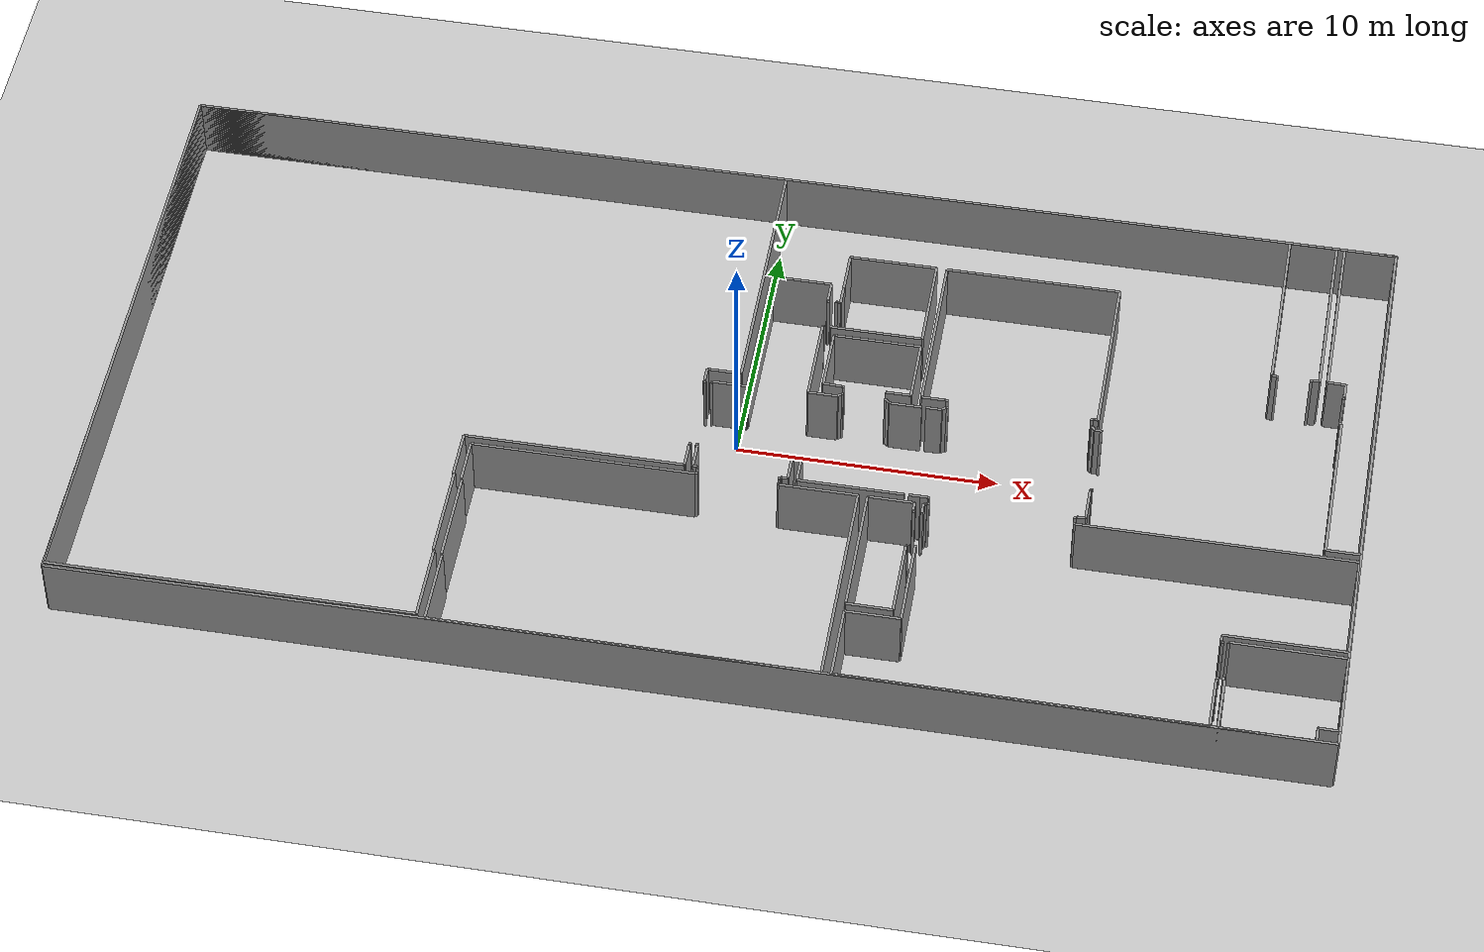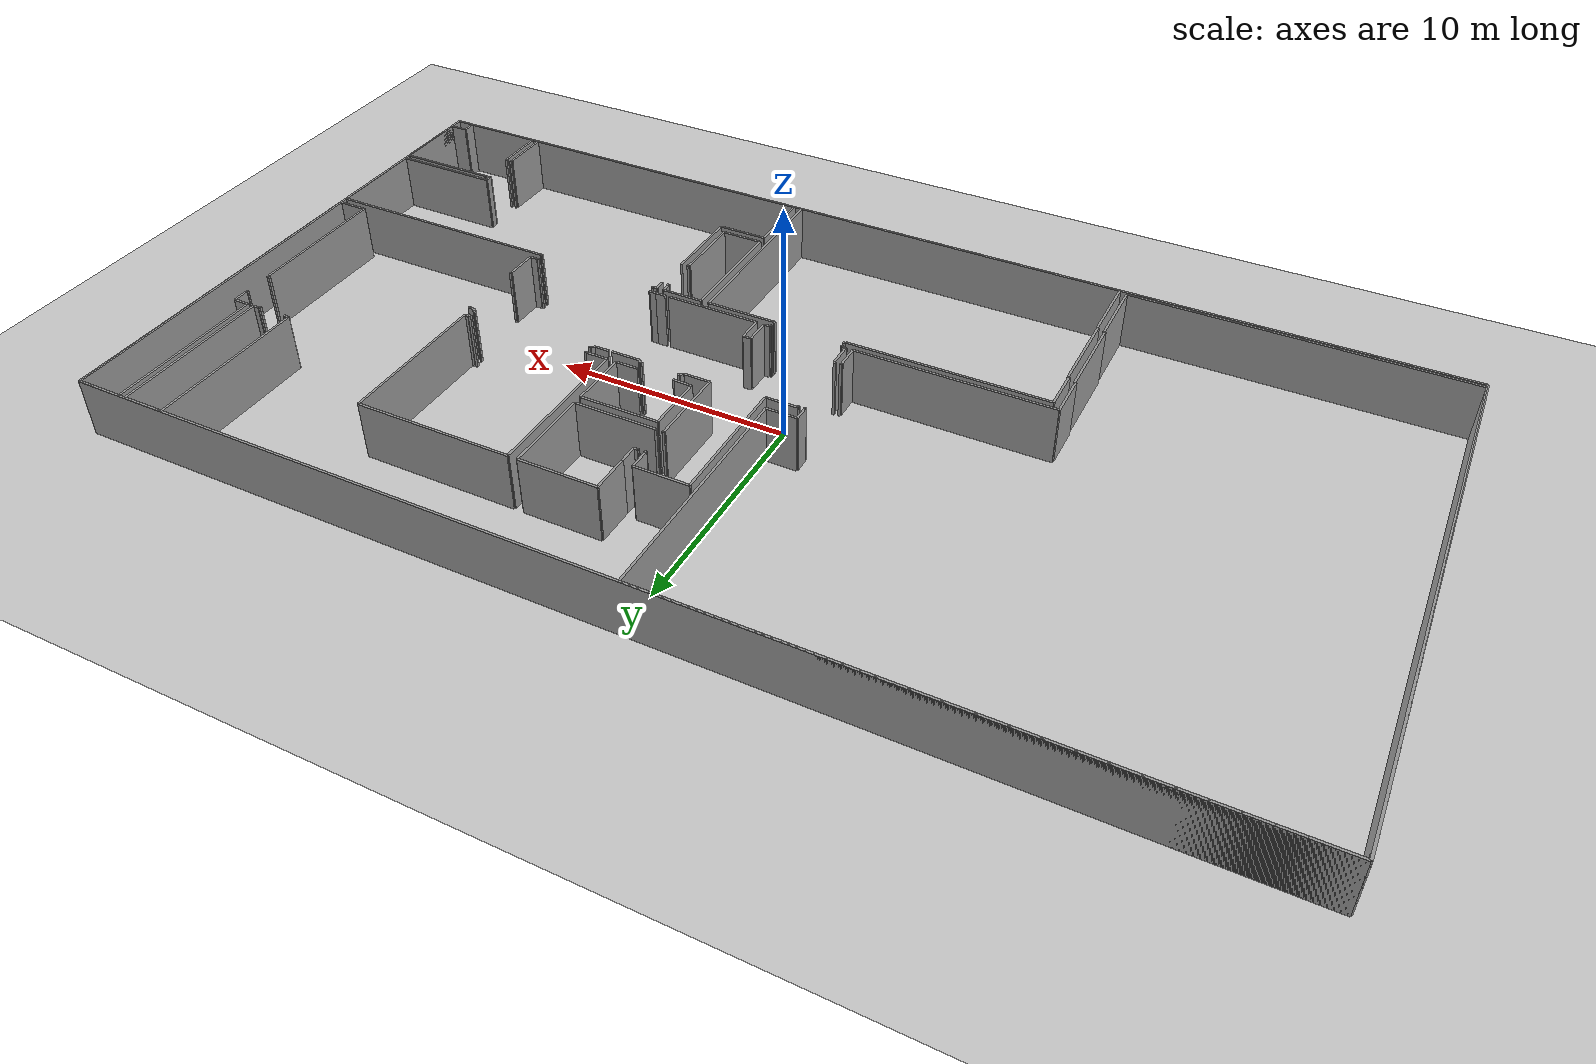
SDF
<sdf version="1.6">
  <world name="default">
    <light name="sun" type="directional">
      <cast_shadows>1</cast_shadows>
      <pose frame="">0 0 10 0 -0 0</pose>
      <diffuse>0.8 0.8 0.8 1</diffuse>
      <specular>0.1 0.1 0.1 1</specular>
      <attenuation>
        <range>1000</range>
        <constant>0.9</constant>
        <linear>0.01</linear>
        <quadratic>0.001</quadratic>
      </attenuation>
      <direction>-0.5 0.5 -1</direction>
    </light>
    <model name="ground_plane">
      <static>1</static>
      <link name="link">
        <collision name="collision">
          <geometry>
            <plane>
              <normal>0 0 1</normal>
              <size>100 100</size>
            </plane>
          </geometry>
          <surface>
            <friction>
              <ode>
                <mu>100</mu>
                <mu2>50</mu2>
              </ode>
              <torsional>
                <ode />
              </torsional>
            </friction>
            <contact>
              <ode />
            </contact>
            <bounce />
          </surface>
          <max_contacts>10</max_contacts>
        </collision>
        <visual name="visual">
          <cast_shadows>0</cast_shadows>
          <geometry>
            <plane>
              <normal>0 0 1</normal>
              <size>100 100</size>
            </plane>
          </geometry>
          <material>
            <script>
              <uri>file://media/materials/scripts/gazebo.material</uri>
              <name>Gazebo/Grey</name>
            </script>
          </material>
        </visual>
        <self_collide>0</self_collide>
        <kinematic>0</kinematic>
        <gravity>1</gravity>
      </link>
    </model>
    <gravity>0 0 -9.8</gravity>
    <magnetic_field>6e-06 2.3e-05 -4.2e-05</magnetic_field>
    <atmosphere type="adiabatic" />
    <physics default="0" name="default_physics" type="ode">
      <max_step_size>0.001</max_step_size>
      <real_time_factor>1</real_time_factor>
      <real_time_update_rate>1000</real_time_update_rate>
    </physics>
    <scene>
      <ambient>0.4 0.4 0.4 1</ambient>
      <background>0.7 0.7 0.7 1</background>
      <shadows>1</shadows>
    </scene>
    <spherical_coordinates>
      <surface_model>EARTH_WGS84</surface_model>
      <latitude_deg>0</latitude_deg>
      <longitude_deg>0</longitude_deg>
      <elevation>0</elevation>
      <heading_deg>0</heading_deg>
    </spherical_coordinates>
  <model name="0510030940_A_40_1_104">
		<static>1</static>
		<link name="Wall_0">
			<collision name="Wall_0_Collision">
				<geometry>
					<box>
						<size>23.7750330385 0.1 2.5</size>
					</box>
				</geometry>
				<pose frame="">11.8875165193 0 1.25 0 0 0</pose>
			</collision>
			<visual name="Wall_0_Visual">
				<pose frame="">11.8875165193 0 1.25 0 0 0</pose>
				<geometry>
					<box>
						<size>23.7750330385 0.1 2.5</size>
					</box>
				</geometry>
				<material>
					<script>
						<uri>file://media/materials/scripts/gazebo.material</uri>
						<name>Gazebo/Grey</name>
					</script>
					<ambient>1 1 1 1</ambient>
				</material>
			</visual>
			<pose frame="">0.0 -23.7750330385 0 0 0 1.57079632679</pose>
		</link>
		<link name="Wall_1">
			<collision name="Wall_1_Collision">
				<geometry>
					<box>
						<size>23.6292823015 0.1 2.5</size>
					</box>
				</geometry>
				<pose frame="">11.8146411508 0 1.25 0 0 0</pose>
			</collision>
			<visual name="Wall_1_Visual">
				<pose frame="">11.8146411508 0 1.25 0 0 0</pose>
				<geometry>
					<box>
						<size>23.6292823015 0.1 2.5</size>
					</box>
				</geometry>
				<material>
					<script>
						<uri>file://media/materials/scripts/gazebo.material</uri>
						<name>Gazebo/Grey</name>
					</script>
					<ambient>1 1 1 1</ambient>
				</material>
			</visual>
			<pose frame="">0.0 -0.0 0 0 0 0.0</pose>
		</link>
		<link name="Wall_2">
			<collision name="Wall_2_Collision">
				<geometry>
					<box>
						<size>10.2911202602 0.1 2.5</size>
					</box>
				</geometry>
				<pose frame="">5.14556013012 0 1.25 0 0 0</pose>
			</collision>
			<visual name="Wall_2_Visual">
				<pose frame="">5.14556013012 0 1.25 0 0 0</pose>
				<geometry>
					<box>
						<size>10.2911202602 0.1 2.5</size>
					</box>
				</geometry>
				<material>
					<script>
						<uri>file://media/materials/scripts/gazebo.material</uri>
						<name>Gazebo/Grey</name>
					</script>
					<ambient>1 1 1 1</ambient>
				</material>
			</visual>
			<pose frame="">23.6292823015 -0.0 0 0 0 -1.57079632679</pose>
		</link>
		<link name="Wall_3">
			<collision name="Wall_3_Collision">
				<geometry>
					<box>
						<size>1.30629256887 0.1 2.5</size>
					</box>
				</geometry>
				<pose frame="">0.653146284436 0 1.25 0 0 0</pose>
			</collision>
			<visual name="Wall_3_Visual">
				<pose frame="">0.653146284436 0 1.25 0 0 0</pose>
				<geometry>
					<box>
						<size>1.30629256887 0.1 2.5</size>
					</box>
				</geometry>
				<material>
					<script>
						<uri>file://media/materials/scripts/gazebo.material</uri>
						<name>Gazebo/Grey</name>
					</script>
					<ambient>1 1 1 1</ambient>
				</material>
			</visual>
			<pose frame="">23.6292823015 -10.2911202602 0 0 0 3.14159265359</pose>
		</link>
		<link name="Wall_4">
			<collision name="Wall_4_Collision">
				<geometry>
					<box>
						<size>0.621886754092 0.1 2.5</size>
					</box>
				</geometry>
				<pose frame="">0.310943377046 0 1.25 0 0 0</pose>
			</collision>
			<visual name="Wall_4_Visual">
				<pose frame="">0.310943377046 0 1.25 0 0 0</pose>
				<geometry>
					<box>
						<size>0.621886754092 0.1 2.5</size>
					</box>
				</geometry>
				<material>
					<script>
						<uri>file://media/materials/scripts/gazebo.material</uri>
						<name>Gazebo/Grey</name>
					</script>
					<ambient>1 1 1 1</ambient>
				</material>
			</visual>
			<pose frame="">22.3229897326 -10.2911202602 0 0 0 -1.57079632679</pose>
		</link>
		<link name="Wall_5">
			<collision name="Wall_5_Collision">
				<geometry>
					<box>
						<size>0.0238893971739 0.1 2.5</size>
					</box>
				</geometry>
				<pose frame="">0.011944698587 0 1.25 0 0 0</pose>
			</collision>
			<visual name="Wall_5_Visual">
				<pose frame="">0.011944698587 0 1.25 0 0 0</pose>
				<geometry>
					<box>
						<size>0.0238893971739 0.1 2.5</size>
					</box>
				</geometry>
				<material>
					<script>
						<uri>file://media/materials/scripts/gazebo.material</uri>
						<name>Gazebo/Grey</name>
					</script>
					<ambient>1 1 1 1</ambient>
				</material>
			</visual>
			<pose frame="">22.3229897326 -10.9130070143 0 0 0 0.0</pose>
		</link>
		<link name="Wall_6">
			<collision name="Wall_6_Collision">
				<geometry>
					<box>
						<size>0.0852648165091 0.1 2.5</size>
					</box>
				</geometry>
				<pose frame="">0.0426324082545 0 1.25 0 0 0</pose>
			</collision>
			<visual name="Wall_6_Visual">
				<pose frame="">0.0426324082545 0 1.25 0 0 0</pose>
				<geometry>
					<box>
						<size>0.0852648165091 0.1 2.5</size>
					</box>
				</geometry>
				<material>
					<script>
						<uri>file://media/materials/scripts/gazebo.material</uri>
						<name>Gazebo/Grey</name>
					</script>
					<ambient>1 1 1 1</ambient>
				</material>
			</visual>
			<pose frame="">22.3468791298 -10.9130070143 0 0 0 -1.57079632679</pose>
		</link>
		<link name="Wall_7">
			<collision name="Wall_7_Collision">
				<geometry>
					<box>
						<size>0.0827233912778 0.1 2.5</size>
					</box>
				</geometry>
				<pose frame="">0.0413616956389 0 1.25 0 0 0</pose>
			</collision>
			<visual name="Wall_7_Visual">
				<pose frame="">0.0413616956389 0 1.25 0 0 0</pose>
				<geometry>
					<box>
						<size>0.0827233912778 0.1 2.5</size>
					</box>
				</geometry>
				<material>
					<script>
						<uri>file://media/materials/scripts/gazebo.material</uri>
						<name>Gazebo/Grey</name>
					</script>
					<ambient>1 1 1 1</ambient>
				</material>
			</visual>
			<pose frame="">22.3468791298 -14.0210430009 0 0 0 -1.57079632679</pose>
		</link>
		<link name="Wall_8">
			<collision name="Wall_8_Collision">
				<geometry>
					<box>
						<size>0.0255413235743 0.1 2.5</size>
					</box>
				</geometry>
				<pose frame="">0.0127706617871 0 1.25 0 0 0</pose>
			</collision>
			<visual name="Wall_8_Visual">
				<pose frame="">0.0127706617871 0 1.25 0 0 0</pose>
				<geometry>
					<box>
						<size>0.0255413235743 0.1 2.5</size>
					</box>
				</geometry>
				<material>
					<script>
						<uri>file://media/materials/scripts/gazebo.material</uri>
						<name>Gazebo/Grey</name>
					</script>
					<ambient>1 1 1 1</ambient>
				</material>
			</visual>
			<pose frame="">22.3468791298 -14.1037663922 0 0 0 3.14159265359</pose>
		</link>
		<link name="Wall_9">
			<collision name="Wall_9_Collision">
				<geometry>
					<box>
						<size>1.01987394531 0.1 2.5</size>
					</box>
				</geometry>
				<pose frame="">0.509936972654 0 1.25 0 0 0</pose>
			</collision>
			<visual name="Wall_9_Visual">
				<pose frame="">0.509936972654 0 1.25 0 0 0</pose>
				<geometry>
					<box>
						<size>1.01987394531 0.1 2.5</size>
					</box>
				</geometry>
				<material>
					<script>
						<uri>file://media/materials/scripts/gazebo.material</uri>
						<name>Gazebo/Grey</name>
					</script>
					<ambient>1 1 1 1</ambient>
				</material>
			</visual>
			<pose frame="">22.3213378062 -14.1037663922 0 0 0 -1.57079632679</pose>
		</link>
		<link name="Wall_10">
			<collision name="Wall_10_Collision">
				<geometry>
					<box>
						<size>8.40322252719 0.1 2.5</size>
					</box>
				</geometry>
				<pose frame="">4.2016112636 0 1.25 0 0 0</pose>
			</collision>
			<visual name="Wall_10_Visual">
				<pose frame="">4.2016112636 0 1.25 0 0 0</pose>
				<geometry>
					<box>
						<size>8.40322252719 0.1 2.5</size>
					</box>
				</geometry>
				<material>
					<script>
						<uri>file://media/materials/scripts/gazebo.material</uri>
						<name>Gazebo/Grey</name>
					</script>
					<ambient>1 1 1 1</ambient>
				</material>
			</visual>
			<pose frame="">22.3213378062 -15.1236403375 0 0 0 3.14159265359</pose>
		</link>
		<link name="Wall_11">
			<collision name="Wall_11_Collision">
				<geometry>
					<box>
						<size>1.89107451459 0.1 2.5</size>
					</box>
				</geometry>
				<pose frame="">0.945537257294 0 1.25 0 0 0</pose>
			</collision>
			<visual name="Wall_11_Visual">
				<pose frame="">0.945537257294 0 1.25 0 0 0</pose>
				<geometry>
					<box>
						<size>1.89107451459 0.1 2.5</size>
					</box>
				</geometry>
				<material>
					<script>
						<uri>file://media/materials/scripts/gazebo.material</uri>
						<name>Gazebo/Grey</name>
					</script>
					<ambient>1 1 1 1</ambient>
				</material>
			</visual>
			<pose frame="">13.918115279 -15.1236403375 0 0 0 -1.57079632679</pose>
		</link>
		<link name="Wall_12">
			<collision name="Wall_12_Collision">
				<geometry>
					<box>
						<size>0.0388838060384 0.1 2.5</size>
					</box>
				</geometry>
				<pose frame="">0.0194419030192 0 1.25 0 0 0</pose>
			</collision>
			<visual name="Wall_12_Visual">
				<pose frame="">0.0194419030192 0 1.25 0 0 0</pose>
				<geometry>
					<box>
						<size>0.0388838060384 0.1 2.5</size>
					</box>
				</geometry>
				<material>
					<script>
						<uri>file://media/materials/scripts/gazebo.material</uri>
						<name>Gazebo/Grey</name>
					</script>
					<ambient>1 1 1 1</ambient>
				</material>
			</visual>
			<pose frame="">13.918115279 -17.0147148521 0 0 0 0.0</pose>
		</link>
		<link name="Wall_13">
			<collision name="Wall_13_Collision">
				<geometry>
					<box>
						<size>3.72509403273 0.1 2.5</size>
					</box>
				</geometry>
				<pose frame="">1.86254701637 0 1.25 0 0 0</pose>
			</collision>
			<visual name="Wall_13_Visual">
				<pose frame="">1.86254701637 0 1.25 0 0 0</pose>
				<geometry>
					<box>
						<size>3.72509403273 0.1 2.5</size>
					</box>
				</geometry>
				<material>
					<script>
						<uri>file://media/materials/scripts/gazebo.material</uri>
						<name>Gazebo/Grey</name>
					</script>
					<ambient>1 1 1 1</ambient>
				</material>
			</visual>
			<pose frame="">13.9569990851 -17.0147148521 0 0 0 -1.57079632679</pose>
		</link>
		<link name="Wall_14">
			<collision name="Wall_14_Collision">
				<geometry>
					<box>
						<size>0.0386296635153 0.1 2.5</size>
					</box>
				</geometry>
				<pose frame="">0.0193148317576 0 1.25 0 0 0</pose>
			</collision>
			<visual name="Wall_14_Visual">
				<pose frame="">0.0193148317576 0 1.25 0 0 0</pose>
				<geometry>
					<box>
						<size>0.0386296635153 0.1 2.5</size>
					</box>
				</geometry>
				<material>
					<script>
						<uri>file://media/materials/scripts/gazebo.material</uri>
						<name>Gazebo/Grey</name>
					</script>
					<ambient>1 1 1 1</ambient>
				</material>
			</visual>
			<pose frame="">13.9569990851 -20.7398088848 0 0 0 0.0</pose>
		</link>
		<link name="Wall_15">
			<collision name="Wall_15_Collision">
				<geometry>
					<box>
						<size>3.04043407543 0.1 2.5</size>
					</box>
				</geometry>
				<pose frame="">1.52021703771 0 1.25 0 0 0</pose>
			</collision>
			<visual name="Wall_15_Visual">
				<pose frame="">1.52021703771 0 1.25 0 0 0</pose>
				<geometry>
					<box>
						<size>3.04043407543 0.1 2.5</size>
					</box>
				</geometry>
				<material>
					<script>
						<uri>file://media/materials/scripts/gazebo.material</uri>
						<name>Gazebo/Grey</name>
					</script>
					<ambient>1 1 1 1</ambient>
				</material>
			</visual>
			<pose frame="">13.9956287486 -20.7398088848 0 0 0 -1.57079632679</pose>
		</link>
		<link name="Wall_16">
			<collision name="Wall_16_Collision">
				<geometry>
					<box>
						<size>13.9956297183 0.1 2.5</size>
					</box>
				</geometry>
				<pose frame="">6.99781485915 0 1.25 0 0 0</pose>
			</collision>
			<visual name="Wall_16_Visual">
				<pose frame="">6.99781485915 0 1.25 0 0 0</pose>
				<geometry>
					<box>
						<size>13.9956297183 0.1 2.5</size>
					</box>
				</geometry>
				<material>
					<script>
						<uri>file://media/materials/scripts/gazebo.material</uri>
						<name>Gazebo/Grey</name>
					</script>
					<ambient>1 1 1 1</ambient>
				</material>
			</visual>
			<pose frame="">13.9956287486 -23.7802429603 0 0 0 3.14122040011</pose>
		</link>
		<link name="Wall_17">
			<collision name="Wall_17_Collision">
				<geometry>
					<box>
						<size>0.977813357731 0.1 2.5</size>
					</box>
				</geometry>
				<pose frame="">0.488906678866 0 1.25 0 0 0</pose>
			</collision>
			<visual name="Wall_17_Visual">
				<pose frame="">0.488906678866 0 1.25 0 0 0</pose>
				<geometry>
					<box>
						<size>0.977813357731 0.1 2.5</size>
					</box>
				</geometry>
				<material>
					<script>
						<uri>file://media/materials/scripts/gazebo.material</uri>
						<name>Gazebo/Grey</name>
					</script>
					<ambient>1 1 1 1</ambient>
				</material>
			</visual>
			<pose frame="">22.6310104707 -15.0811985361 0 0 0 1.57079632679</pose>
		</link>
		<link name="Wall_18">
			<collision name="Wall_18_Collision">
				<geometry>
					<box>
						<size>0.0330385280065 0.1 2.5</size>
					</box>
				</geometry>
				<pose frame="">0.0165192640033 0 1.25 0 0 0</pose>
			</collision>
			<visual name="Wall_18_Visual">
				<pose frame="">0.0165192640033 0 1.25 0 0 0</pose>
				<geometry>
					<box>
						<size>0.0330385280065 0.1 2.5</size>
					</box>
				</geometry>
				<material>
					<script>
						<uri>file://media/materials/scripts/gazebo.material</uri>
						<name>Gazebo/Grey</name>
					</script>
					<ambient>1 1 1 1</ambient>
				</material>
			</visual>
			<pose frame="">22.6310104707 -14.1033851784 0 0 0 3.14159265359</pose>
		</link>
		<link name="Wall_19">
			<collision name="Wall_19_Collision">
				<geometry>
					<box>
						<size>0.104452577005 0.1 2.5</size>
					</box>
				</geometry>
				<pose frame="">0.0522262885026 0 1.25 0 0 0</pose>
			</collision>
			<visual name="Wall_19_Visual">
				<pose frame="">0.0522262885026 0 1.25 0 0 0</pose>
				<geometry>
					<box>
						<size>0.104452577005 0.1 2.5</size>
					</box>
				</geometry>
				<material>
					<script>
						<uri>file://media/materials/scripts/gazebo.material</uri>
						<name>Gazebo/Grey</name>
					</script>
					<ambient>1 1 1 1</ambient>
				</material>
			</visual>
			<pose frame="">22.5979719427 -14.1033851784 0 0 0 1.57079632679</pose>
		</link>
		<link name="Wall_20">
			<collision name="Wall_20_Collision">
				<geometry>
					<box>
						<size>0.0955575886957 0.1 2.5</size>
					</box>
				</geometry>
				<pose frame="">0.0477787943479 0 1.25 0 0 0</pose>
			</collision>
			<visual name="Wall_20_Visual">
				<pose frame="">0.0477787943479 0 1.25 0 0 0</pose>
				<geometry>
					<box>
						<size>0.0955575886957 0.1 2.5</size>
					</box>
				</geometry>
				<material>
					<script>
						<uri>file://media/materials/scripts/gazebo.material</uri>
						<name>Gazebo/Grey</name>
					</script>
					<ambient>1 1 1 1</ambient>
				</material>
			</visual>
			<pose frame="">22.5979719427 -10.9724763647 0 0 0 1.57079632679</pose>
		</link>
		<link name="Wall_21">
			<collision name="Wall_21_Collision">
				<geometry>
					<box>
						<size>1.35801057233 0.1 2.5</size>
					</box>
				</geometry>
				<pose frame="">0.679005286164 0 1.25 0 0 0</pose>
			</collision>
			<visual name="Wall_21_Visual">
				<pose frame="">0.679005286164 0 1.25 0 0 0</pose>
				<geometry>
					<box>
						<size>1.35801057233 0.1 2.5</size>
					</box>
				</geometry>
				<material>
					<script>
						<uri>file://media/materials/scripts/gazebo.material</uri>
						<name>Gazebo/Grey</name>
					</script>
					<ambient>1 1 1 1</ambient>
				</material>
			</visual>
			<pose frame="">22.5979719427 -10.876918776 0 0 0 0.0</pose>
		</link>
		<link name="Wall_22">
			<collision name="Wall_22_Collision">
				<geometry>
					<box>
						<size>5.69139473417 0.1 2.5</size>
					</box>
				</geometry>
				<pose frame="">2.84569736708 0 1.25 0 0 0</pose>
			</collision>
			<visual name="Wall_22_Visual">
				<pose frame="">2.84569736708 0 1.25 0 0 0</pose>
				<geometry>
					<box>
						<size>5.69139473417 0.1 2.5</size>
					</box>
				</geometry>
				<material>
					<script>
						<uri>file://media/materials/scripts/gazebo.material</uri>
						<name>Gazebo/Grey</name>
					</script>
					<ambient>1 1 1 1</ambient>
				</material>
			</visual>
			<pose frame="">23.955982515 -10.876918776 0 0 0 1.57079632679</pose>
		</link>
		<link name="Wall_23">
			<collision name="Wall_23_Collision">
				<geometry>
					<box>
						<size>2.30519975602 0.1 2.5</size>
					</box>
				</geometry>
				<pose frame="">1.15259987801 0 1.25 0 0 0</pose>
			</collision>
			<visual name="Wall_23_Visual">
				<pose frame="">1.15259987801 0 1.25 0 0 0</pose>
				<geometry>
					<box>
						<size>2.30519975602 0.1 2.5</size>
					</box>
				</geometry>
				<material>
					<script>
						<uri>file://media/materials/scripts/gazebo.material</uri>
						<name>Gazebo/Grey</name>
					</script>
					<ambient>1 1 1 1</ambient>
				</material>
			</visual>
			<pose frame="">23.955982515 -5.18552404188 0 0 0 0.0</pose>
		</link>
		<link name="Wall_24">
			<collision name="Wall_24_Collision">
				<geometry>
					<box>
						<size>0.864465792416 0.1 2.5</size>
					</box>
				</geometry>
				<pose frame="">0.432232896208 0 1.25 0 0 0</pose>
			</collision>
			<visual name="Wall_24_Visual">
				<pose frame="">0.432232896208 0 1.25 0 0 0</pose>
				<geometry>
					<box>
						<size>0.864465792416 0.1 2.5</size>
					</box>
				</geometry>
				<material>
					<script>
						<uri>file://media/materials/scripts/gazebo.material</uri>
						<name>Gazebo/Grey</name>
					</script>
					<ambient>1 1 1 1</ambient>
				</material>
			</visual>
			<pose frame="">26.261182271 -5.18552404188 0 0 0 -1.57079632679</pose>
		</link>
		<link name="Wall_25">
			<collision name="Wall_25_Collision">
				<geometry>
					<box>
						<size>0.0363423808072 0.1 2.5</size>
					</box>
				</geometry>
				<pose frame="">0.0181711904036 0 1.25 0 0 0</pose>
			</collision>
			<visual name="Wall_25_Visual">
				<pose frame="">0.0181711904036 0 1.25 0 0 0</pose>
				<geometry>
					<box>
						<size>0.0363423808072 0.1 2.5</size>
					</box>
				</geometry>
				<material>
					<script>
						<uri>file://media/materials/scripts/gazebo.material</uri>
						<name>Gazebo/Grey</name>
					</script>
					<ambient>1 1 1 1</ambient>
				</material>
			</visual>
			<pose frame="">26.261182271 -6.0499898343 0 0 0 0.0</pose>
		</link>
		<link name="Wall_26">
			<collision name="Wall_26_Collision">
				<geometry>
					<box>
						<size>0.079165395954 0.1 2.5</size>
					</box>
				</geometry>
				<pose frame="">0.039582697977 0 1.25 0 0 0</pose>
			</collision>
			<visual name="Wall_26_Visual">
				<pose frame="">0.039582697977 0 1.25 0 0 0</pose>
				<geometry>
					<box>
						<size>0.079165395954 0.1 2.5</size>
					</box>
				</geometry>
				<material>
					<script>
						<uri>file://media/materials/scripts/gazebo.material</uri>
						<name>Gazebo/Grey</name>
					</script>
					<ambient>1 1 1 1</ambient>
				</material>
			</visual>
			<pose frame="">26.2975246518 -6.0499898343 0 0 0 -1.57079632679</pose>
		</link>
		<link name="Wall_27">
			<collision name="Wall_27_Collision">
				<geometry>
					<box>
						<size>0.0738284029684 0.1 2.5</size>
					</box>
				</geometry>
				<pose frame="">0.0369142014842 0 1.25 0 0 0</pose>
			</collision>
			<visual name="Wall_27_Visual">
				<pose frame="">0.0369142014842 0 1.25 0 0 0</pose>
				<geometry>
					<box>
						<size>0.0738284029684 0.1 2.5</size>
					</box>
				</geometry>
				<material>
					<script>
						<uri>file://media/materials/scripts/gazebo.material</uri>
						<name>Gazebo/Grey</name>
					</script>
					<ambient>1 1 1 1</ambient>
				</material>
			</visual>
			<pose frame="">26.2975246518 -7.33086815086 0 0 0 -1.57079632679</pose>
		</link>
		<link name="Wall_28">
			<collision name="Wall_28_Collision">
				<geometry>
					<box>
						<size>0.0190606892345 0.1 2.5</size>
					</box>
				</geometry>
				<pose frame="">0.00953034461726 0 1.25 0 0 0</pose>
			</collision>
			<visual name="Wall_28_Visual">
				<pose frame="">0.00953034461726 0 1.25 0 0 0</pose>
				<geometry>
					<box>
						<size>0.0190606892345 0.1 2.5</size>
					</box>
				</geometry>
				<material>
					<script>
						<uri>file://media/materials/scripts/gazebo.material</uri>
						<name>Gazebo/Grey</name>
					</script>
					<ambient>1 1 1 1</ambient>
				</material>
			</visual>
			<pose frame="">26.2975246518 -7.40469655383 0 0 0 3.14159265359</pose>
		</link>
		<link name="Wall_29">
			<collision name="Wall_29_Collision">
				<geometry>
					<box>
						<size>3.37717291857 0.1 2.5</size>
					</box>
				</geometry>
				<pose frame="">1.68858645929 0 1.25 0 0 0</pose>
			</collision>
			<visual name="Wall_29_Visual">
				<pose frame="">1.68858645929 0 1.25 0 0 0</pose>
				<geometry>
					<box>
						<size>3.37717291857 0.1 2.5</size>
					</box>
				</geometry>
				<material>
					<script>
						<uri>file://media/materials/scripts/gazebo.material</uri>
						<name>Gazebo/Grey</name>
					</script>
					<ambient>1 1 1 1</ambient>
				</material>
			</visual>
			<pose frame="">26.2784639626 -7.40469655383 0 0 0 -1.57079632679</pose>
		</link>
		<link name="Wall_30">
			<collision name="Wall_30_Collision">
				<geometry>
					<box>
						<size>1.12534309241 0.1 2.5</size>
					</box>
				</geometry>
				<pose frame="">0.562671546203 0 1.25 0 0 0</pose>
			</collision>
			<visual name="Wall_30_Visual">
				<pose frame="">0.562671546203 0 1.25 0 0 0</pose>
				<geometry>
					<box>
						<size>1.12534309241 0.1 2.5</size>
					</box>
				</geometry>
				<material>
					<script>
						<uri>file://media/materials/scripts/gazebo.material</uri>
						<name>Gazebo/Grey</name>
					</script>
					<ambient>1 1 1 1</ambient>
				</material>
			</visual>
			<pose frame="">26.2784639626 -10.7818694724 0 0 0 0.0</pose>
		</link>
		<link name="Wall_31">
			<collision name="Wall_31_Collision">
				<geometry>
					<box>
						<size>0.172371779898 0.1 2.5</size>
					</box>
				</geometry>
				<pose frame="">0.0861858899488 0 1.25 0 0 0</pose>
			</collision>
			<visual name="Wall_31_Visual">
				<pose frame="">0.0861858899488 0 1.25 0 0 0</pose>
				<geometry>
					<box>
						<size>0.172371779898 0.1 2.5</size>
					</box>
				</geometry>
				<material>
					<script>
						<uri>file://media/materials/scripts/gazebo.material</uri>
						<name>Gazebo/Grey</name>
					</script>
					<ambient>1 1 1 1</ambient>
				</material>
			</visual>
			<pose frame="">27.403807055 -10.7818694724 0 0 0 0.805207876201</pose>
		</link>
		<link name="Wall_32">
			<collision name="Wall_32_Collision">
				<geometry>
					<box>
						<size>0.0859001728169 0.1 2.5</size>
					</box>
				</geometry>
				<pose frame="">0.0429500864085 0 1.25 0 0 0</pose>
			</collision>
			<visual name="Wall_32_Visual">
				<pose frame="">0.0429500864085 0 1.25 0 0 0</pose>
				<geometry>
					<box>
						<size>0.0859001728169 0.1 2.5</size>
					</box>
				</geometry>
				<material>
					<script>
						<uri>file://media/materials/scripts/gazebo.material</uri>
						<name>Gazebo/Grey</name>
					</script>
					<ambient>1 1 1 1</ambient>
				</material>
			</visual>
			<pose frame="">27.5232540409 -10.6575937786 0 0 0 0.0</pose>
		</link>
		<link name="Wall_33">
			<collision name="Wall_33_Collision">
				<geometry>
					<box>
						<size>0.0825963200163 0.1 2.5</size>
					</box>
				</geometry>
				<pose frame="">0.0412981600081 0 1.25 0 0 0</pose>
			</collision>
			<visual name="Wall_33_Visual">
				<pose frame="">0.0412981600081 0 1.25 0 0 0</pose>
				<geometry>
					<box>
						<size>0.0825963200163 0.1 2.5</size>
					</box>
				</geometry>
				<material>
					<script>
						<uri>file://media/materials/scripts/gazebo.material</uri>
						<name>Gazebo/Grey</name>
					</script>
					<ambient>1 1 1 1</ambient>
				</material>
			</visual>
			<pose frame="">29.1739097286 -10.6575937786 0 0 0 0.0</pose>
		</link>
		<link name="Wall_34">
			<collision name="Wall_34_Collision">
				<geometry>
					<box>
						<size>0.185640458335 0.1 2.5</size>
					</box>
				</geometry>
				<pose frame="">0.0928202291675 0 1.25 0 0 0</pose>
			</collision>
			<visual name="Wall_34_Visual">
				<pose frame="">0.0928202291675 0 1.25 0 0 0</pose>
				<geometry>
					<box>
						<size>0.185640458335 0.1 2.5</size>
					</box>
				</geometry>
				<material>
					<script>
						<uri>file://media/materials/scripts/gazebo.material</uri>
						<name>Gazebo/Grey</name>
					</script>
					<ambient>1 1 1 1</ambient>
				</material>
			</visual>
			<pose frame="">29.2565060486 -10.6575937786 0 0 0 -0.77862188764</pose>
		</link>
		<link name="Wall_35">
			<collision name="Wall_35_Collision">
				<geometry>
					<box>
						<size>1.23030395446 0.1 2.5</size>
					</box>
				</geometry>
				<pose frame="">0.615151977229 0 1.25 0 0 0</pose>
			</collision>
			<visual name="Wall_35_Visual">
				<pose frame="">0.615151977229 0 1.25 0 0 0</pose>
				<geometry>
					<box>
						<size>1.23030395446 0.1 2.5</size>
					</box>
				</geometry>
				<material>
					<script>
						<uri>file://media/materials/scripts/gazebo.material</uri>
						<name>Gazebo/Grey</name>
					</script>
					<ambient>1 1 1 1</ambient>
				</material>
			</visual>
			<pose frame="">29.3886601606 -10.787968893 0 0 0 0.0</pose>
		</link>
		<link name="Wall_36">
			<collision name="Wall_36_Collision">
				<geometry>
					<box>
						<size>4.05014231981 0.1 2.5</size>
					</box>
				</geometry>
				<pose frame="">2.02507115991 0 1.25 0 0 0</pose>
			</collision>
			<visual name="Wall_36_Visual">
				<pose frame="">2.02507115991 0 1.25 0 0 0</pose>
				<geometry>
					<box>
						<size>4.05014231981 0.1 2.5</size>
					</box>
				</geometry>
				<material>
					<script>
						<uri>file://media/materials/scripts/gazebo.material</uri>
						<name>Gazebo/Grey</name>
					</script>
					<ambient>1 1 1 1</ambient>
				</material>
			</visual>
			<pose frame="">30.6189641151 -15.1343143235 0 0 0 3.14159265359</pose>
		</link>
		<link name="Wall_37">
			<collision name="Wall_37_Collision">
				<geometry>
					<box>
						<size>1.1131442513 0.1 2.5</size>
					</box>
				</geometry>
				<pose frame="">0.556572125648 0 1.25 0 0 0</pose>
			</collision>
			<visual name="Wall_37_Visual">
				<pose frame="">0.556572125648 0 1.25 0 0 0</pose>
				<geometry>
					<box>
						<size>1.1131442513 0.1 2.5</size>
					</box>
				</geometry>
				<material>
					<script>
						<uri>file://media/materials/scripts/gazebo.material</uri>
						<name>Gazebo/Grey</name>
					</script>
					<ambient>1 1 1 1</ambient>
				</material>
			</visual>
			<pose frame="">26.5688217953 -15.1343143235 0 0 0 1.57079632679</pose>
		</link>
		<link name="Wall_38">
			<collision name="Wall_38_Collision">
				<geometry>
					<box>
						<size>0.34220290739 0.1 2.5</size>
					</box>
				</geometry>
				<pose frame="">0.171101453695 0 1.25 0 0 0</pose>
			</collision>
			<visual name="Wall_38_Visual">
				<pose frame="">0.171101453695 0 1.25 0 0 0</pose>
				<geometry>
					<box>
						<size>0.34220290739 0.1 2.5</size>
					</box>
				</geometry>
				<material>
					<script>
						<uri>file://media/materials/scripts/gazebo.material</uri>
						<name>Gazebo/Grey</name>
					</script>
					<ambient>1 1 1 1</ambient>
				</material>
			</visual>
			<pose frame="">26.5688217953 -14.0211700722 0 0 0 3.14159265359</pose>
		</link>
		<link name="Wall_39">
			<collision name="Wall_39_Collision">
				<geometry>
					<box>
						<size>1.08938192538 0.1 2.5</size>
					</box>
				</geometry>
				<pose frame="">0.544690962692 0 1.25 0 0 0</pose>
			</collision>
			<visual name="Wall_39_Visual">
				<pose frame="">0.544690962692 0 1.25 0 0 0</pose>
				<geometry>
					<box>
						<size>1.08938192538 0.1 2.5</size>
					</box>
				</geometry>
				<material>
					<script>
						<uri>file://media/materials/scripts/gazebo.material</uri>
						<name>Gazebo/Grey</name>
					</script>
					<ambient>1 1 1 1</ambient>
				</material>
			</visual>
			<pose frame="">26.2266188879 -14.0211700722 0 0 0 -1.57079632679</pose>
		</link>
		<link name="Wall_40">
			<collision name="Wall_40_Collision">
				<geometry>
					<box>
						<size>0.257954660974 0.1 2.5</size>
					</box>
				</geometry>
				<pose frame="">0.128977330487 0 1.25 0 0 0</pose>
			</collision>
			<visual name="Wall_40_Visual">
				<pose frame="">0.128977330487 0 1.25 0 0 0</pose>
				<geometry>
					<box>
						<size>0.257954660974 0.1 2.5</size>
					</box>
				</geometry>
				<material>
					<script>
						<uri>file://media/materials/scripts/gazebo.material</uri>
						<name>Gazebo/Grey</name>
					</script>
					<ambient>1 1 1 1</ambient>
				</material>
			</visual>
			<pose frame="">26.2266188879 -15.1105519976 0 0 0 3.14159265359</pose>
		</link>
		<link name="Wall_41">
			<collision name="Wall_41_Collision">
				<geometry>
					<box>
						<size>0.062010775643 0.1 2.5</size>
					</box>
				</geometry>
				<pose frame="">0.0310053878215 0 1.25 0 0 0</pose>
			</collision>
			<visual name="Wall_41_Visual">
				<pose frame="">0.0310053878215 0 1.25 0 0 0</pose>
				<geometry>
					<box>
						<size>0.062010775643 0.1 2.5</size>
					</box>
				</geometry>
				<material>
					<script>
						<uri>file://media/materials/scripts/gazebo.material</uri>
						<name>Gazebo/Grey</name>
					</script>
					<ambient>1 1 1 1</ambient>
				</material>
			</visual>
			<pose frame="">25.9686642269 -15.1105519976 0 0 0 -1.57079632679</pose>
		</link>
		<link name="Wall_42">
			<collision name="Wall_42_Collision">
				<geometry>
					<box>
						<size>0.0970824438345 0.1 2.5</size>
					</box>
				</geometry>
				<pose frame="">0.0485412219173 0 1.25 0 0 0</pose>
			</collision>
			<visual name="Wall_42_Visual">
				<pose frame="">0.0485412219173 0 1.25 0 0 0</pose>
				<geometry>
					<box>
						<size>0.0970824438345 0.1 2.5</size>
					</box>
				</geometry>
				<material>
					<script>
						<uri>file://media/materials/scripts/gazebo.material</uri>
						<name>Gazebo/Grey</name>
					</script>
					<ambient>1 1 1 1</ambient>
				</material>
			</visual>
			<pose frame="">25.9686642269 -15.1725627732 0 0 0 3.14159265359</pose>
		</link>
		<link name="Wall_43">
			<collision name="Wall_43_Collision">
				<geometry>
					<box>
						<size>0.0784029683847 0.1 2.5</size>
					</box>
				</geometry>
				<pose frame="">0.0392014841923 0 1.25 0 0 0</pose>
			</collision>
			<visual name="Wall_43_Visual">
				<pose frame="">0.0392014841923 0 1.25 0 0 0</pose>
				<geometry>
					<box>
						<size>0.0784029683847 0.1 2.5</size>
					</box>
				</geometry>
				<material>
					<script>
						<uri>file://media/materials/scripts/gazebo.material</uri>
						<name>Gazebo/Grey</name>
					</script>
					<ambient>1 1 1 1</ambient>
				</material>
			</visual>
			<pose frame="">22.8645674494 -15.1725627732 0 0 0 3.14159265359</pose>
		</link>
		<link name="Wall_44">
			<collision name="Wall_44_Collision">
				<geometry>
					<box>
						<size>0.0482870793941 0.1 2.5</size>
					</box>
				</geometry>
				<pose frame="">0.0241435396971 0 1.25 0 0 0</pose>
			</collision>
			<visual name="Wall_44_Visual">
				<pose frame="">0.0241435396971 0 1.25 0 0 0</pose>
				<geometry>
					<box>
						<size>0.0482870793941 0.1 2.5</size>
					</box>
				</geometry>
				<material>
					<script>
						<uri>file://media/materials/scripts/gazebo.material</uri>
						<name>Gazebo/Grey</name>
					</script>
					<ambient>1 1 1 1</ambient>
				</material>
			</visual>
			<pose frame="">22.786164481 -15.1725627732 0 0 0 1.57079632679</pose>
		</link>
		<link name="Wall_45">
			<collision name="Wall_45_Collision">
				<geometry>
					<box>
						<size>0.156805936769 0.1 2.5</size>
					</box>
				</geometry>
				<pose frame="">0.0784029683847 0 1.25 0 0 0</pose>
			</collision>
			<visual name="Wall_45_Visual">
				<pose frame="">0.0784029683847 0 1.25 0 0 0</pose>
				<geometry>
					<box>
						<size>0.156805936769 0.1 2.5</size>
					</box>
				</geometry>
				<material>
					<script>
						<uri>file://media/materials/scripts/gazebo.material</uri>
						<name>Gazebo/Grey</name>
					</script>
					<ambient>1 1 1 1</ambient>
				</material>
			</visual>
			<pose frame="">22.786164481 -15.1242756938 0 0 0 3.14159265359</pose>
		</link>
		<link name="Wall_46">
			<collision name="Wall_46_Collision">
				<geometry>
					<box>
						<size>0.0431088201388 0.1 2.5</size>
					</box>
				</geometry>
				<pose frame="">0.0215544100694 0 1.25 0 0 0</pose>
			</collision>
			<visual name="Wall_46_Visual">
				<pose frame="">0.0215544100694 0 1.25 0 0 0</pose>
				<geometry>
					<box>
						<size>0.0431088201388 0.1 2.5</size>
					</box>
				</geometry>
				<material>
					<script>
						<uri>file://media/materials/scripts/gazebo.material</uri>
						<name>Gazebo/Grey</name>
					</script>
					<ambient>1 1 1 1</ambient>
				</material>
			</visual>
			<pose frame="">22.6293585443 -15.1242756938 0 0 0 1.53246702555</pose>
		</link>
		<link name="Wall_47">
			<collision name="Wall_47_Collision">
				<geometry>
					<box>
						<size>2.99532377757 0.1 2.5</size>
					</box>
				</geometry>
				<pose frame="">1.49766188879 0 1.25 0 0 0</pose>
			</collision>
			<visual name="Wall_47_Visual">
				<pose frame="">1.49766188879 0 1.25 0 0 0</pose>
				<geometry>
					<box>
						<size>2.99532377757 0.1 2.5</size>
					</box>
				</geometry>
				<material>
					<script>
						<uri>file://media/materials/scripts/gazebo.material</uri>
						<name>Gazebo/Grey</name>
					</script>
					<ambient>1 1 1 1</ambient>
				</material>
			</visual>
			<pose frame="">14.3270305988 -23.9163362814 0 0 0 1.57079632679</pose>
		</link>
		<link name="Wall_48">
			<collision name="Wall_48_Collision">
				<geometry>
					<box>
						<size>0.0325302429603 0.1 2.5</size>
					</box>
				</geometry>
				<pose frame="">0.0162651214801 0 1.25 0 0 0</pose>
			</collision>
			<visual name="Wall_48_Visual">
				<pose frame="">0.0162651214801 0 1.25 0 0 0</pose>
				<geometry>
					<box>
						<size>0.0325302429603 0.1 2.5</size>
					</box>
				</geometry>
				<material>
					<script>
						<uri>file://media/materials/scripts/gazebo.material</uri>
						<name>Gazebo/Grey</name>
					</script>
					<ambient>1 1 1 1</ambient>
				</material>
			</visual>
			<pose frame="">14.3270305988 -20.9210125038 0 0 0 3.14159265359</pose>
		</link>
		<link name="Wall_49">
			<collision name="Wall_49_Collision">
				<geometry>
					<box>
						<size>3.67083460405 0.1 2.5</size>
					</box>
				</geometry>
				<pose frame="">1.83541730202 0 1.25 0 0 0</pose>
			</collision>
			<visual name="Wall_49_Visual">
				<pose frame="">1.83541730202 0 1.25 0 0 0</pose>
				<geometry>
					<box>
						<size>3.67083460405 0.1 2.5</size>
					</box>
				</geometry>
				<material>
					<script>
						<uri>file://media/materials/scripts/gazebo.material</uri>
						<name>Gazebo/Grey</name>
					</script>
					<ambient>1 1 1 1</ambient>
				</material>
			</visual>
			<pose frame="">14.2945003558 -20.9210125038 0 0 0 1.57079632679</pose>
		</link>
		<link name="Wall_50">
			<collision name="Wall_50_Collision">
				<geometry>
					<box>
						<size>0.0400274473925 0.1 2.5</size>
					</box>
				</geometry>
				<pose frame="">0.0200137236962 0 1.25 0 0 0</pose>
			</collision>
			<visual name="Wall_50_Visual">
				<pose frame="">0.0200137236962 0 1.25 0 0 0</pose>
				<geometry>
					<box>
						<size>0.0400274473925 0.1 2.5</size>
					</box>
				</geometry>
				<material>
					<script>
						<uri>file://media/materials/scripts/gazebo.material</uri>
						<name>Gazebo/Grey</name>
					</script>
					<ambient>1 1 1 1</ambient>
				</material>
			</visual>
			<pose frame="">14.2945003558 -17.2501778998 0 0 0 3.14159265359</pose>
		</link>
		<link name="Wall_51">
			<collision name="Wall_51_Collision">
				<geometry>
					<box>
						<size>1.78204737217 0.1 2.5</size>
					</box>
				</geometry>
				<pose frame="">0.891023686083 0 1.25 0 0 0</pose>
			</collision>
			<visual name="Wall_51_Visual">
				<pose frame="">0.891023686083 0 1.25 0 0 0</pose>
				<geometry>
					<box>
						<size>1.78204737217 0.1 2.5</size>
					</box>
				</geometry>
				<material>
					<script>
						<uri>file://media/materials/scripts/gazebo.material</uri>
						<name>Gazebo/Grey</name>
					</script>
					<ambient>1 1 1 1</ambient>
				</material>
			</visual>
			<pose frame="">14.2544729084 -17.2501778998 0 0 0 1.57079632679</pose>
		</link>
		<link name="Wall_52">
			<collision name="Wall_52_Collision">
				<geometry>
					<box>
						<size>8.51961980279 0.1 2.5</size>
					</box>
				</geometry>
				<pose frame="">4.25980990139 0 1.25 0 0 0</pose>
			</collision>
			<visual name="Wall_52_Visual">
				<pose frame="">4.25980990139 0 1.25 0 0 0</pose>
				<geometry>
					<box>
						<size>8.51961980279 0.1 2.5</size>
					</box>
				</geometry>
				<material>
					<script>
						<uri>file://media/materials/scripts/gazebo.material</uri>
						<name>Gazebo/Grey</name>
					</script>
					<ambient>1 1 1 1</ambient>
				</material>
			</visual>
			<pose frame="">14.2544729084 -15.4681305276 0 0 0 0.0</pose>
		</link>
		<link name="Wall_53">
			<collision name="Wall_53_Collision">
				<geometry>
					<box>
						<size>0.0415523025313 0.1 2.5</size>
					</box>
				</geometry>
				<pose frame="">0.0207761512656 0 1.25 0 0 0</pose>
			</collision>
			<visual name="Wall_53_Visual">
				<pose frame="">0.0207761512656 0 1.25 0 0 0</pose>
				<geometry>
					<box>
						<size>0.0415523025313 0.1 2.5</size>
					</box>
				</geometry>
				<material>
					<script>
						<uri>file://media/materials/scripts/gazebo.material</uri>
						<name>Gazebo/Grey</name>
					</script>
					<ambient>1 1 1 1</ambient>
				</material>
			</visual>
			<pose frame="">22.7740927112 -15.4681305276 0 0 0 1.57079632679</pose>
		</link>
		<link name="Wall_54">
			<collision name="Wall_54_Collision">
				<geometry>
					<box>
						<size>0.109281284945 0.1 2.5</size>
					</box>
				</geometry>
				<pose frame="">0.0546406424723 0 1.25 0 0 0</pose>
			</collision>
			<visual name="Wall_54_Visual">
				<pose frame="">0.0546406424723 0 1.25 0 0 0</pose>
				<geometry>
					<box>
						<size>0.109281284945 0.1 2.5</size>
					</box>
				</geometry>
				<material>
					<script>
						<uri>file://media/materials/scripts/gazebo.material</uri>
						<name>Gazebo/Grey</name>
					</script>
					<ambient>1 1 1 1</ambient>
				</material>
			</visual>
			<pose frame="">22.7740927112 -15.4265782251 0 0 0 0.0</pose>
		</link>
		<link name="Wall_55">
			<collision name="Wall_55_Collision">
				<geometry>
					<box>
						<size>0.0731930466606 0.1 2.5</size>
					</box>
				</geometry>
				<pose frame="">0.0365965233303 0 1.25 0 0 0</pose>
			</collision>
			<visual name="Wall_55_Visual">
				<pose frame="">0.0365965233303 0 1.25 0 0 0</pose>
				<geometry>
					<box>
						<size>0.0731930466606 0.1 2.5</size>
					</box>
				</geometry>
				<material>
					<script>
						<uri>file://media/materials/scripts/gazebo.material</uri>
						<name>Gazebo/Grey</name>
					</script>
					<ambient>1 1 1 1</ambient>
				</material>
			</visual>
			<pose frame="">25.8748856359 -15.4265782251 0 0 0 0.0</pose>
		</link>
		<link name="Wall_56">
			<collision name="Wall_56_Collision">
				<geometry>
					<box>
						<size>0.0386296635153 0.1 2.5</size>
					</box>
				</geometry>
				<pose frame="">0.0193148317577 0 1.25 0 0 0</pose>
			</collision>
			<visual name="Wall_56_Visual">
				<pose frame="">0.0193148317577 0 1.25 0 0 0</pose>
				<geometry>
					<box>
						<size>0.0386296635153 0.1 2.5</size>
					</box>
				</geometry>
				<material>
					<script>
						<uri>file://media/materials/scripts/gazebo.material</uri>
						<name>Gazebo/Grey</name>
					</script>
					<ambient>1 1 1 1</ambient>
				</material>
			</visual>
			<pose frame="">25.9480786825 -15.4265782251 0 0 0 -1.57079632679</pose>
		</link>
		<link name="Wall_57">
			<collision name="Wall_57_Collision">
				<geometry>
					<box>
						<size>2.97994815493 0.1 2.5</size>
					</box>
				</geometry>
				<pose frame="">1.48997407746 0 1.25 0 0 0</pose>
			</collision>
			<visual name="Wall_57_Visual">
				<pose frame="">1.48997407746 0 1.25 0 0 0</pose>
				<geometry>
					<box>
						<size>2.97994815493 0.1 2.5</size>
					</box>
				</geometry>
				<material>
					<script>
						<uri>file://media/materials/scripts/gazebo.material</uri>
						<name>Gazebo/Grey</name>
					</script>
					<ambient>1 1 1 1</ambient>
				</material>
			</visual>
			<pose frame="">25.9480786825 -15.4652078886 0 0 0 0.0</pose>
		</link>
		<link name="Wall_58">
			<collision name="Wall_58_Collision">
				<geometry>
					<box>
						<size>8.4637084477 0.1 2.5</size>
					</box>
				</geometry>
				<pose frame="">4.23185422385 0 1.25 0 0 0</pose>
			</collision>
			<visual name="Wall_58_Visual">
				<pose frame="">4.23185422385 0 1.25 0 0 0</pose>
				<geometry>
					<box>
						<size>8.4637084477 0.1 2.5</size>
					</box>
				</geometry>
				<material>
					<script>
						<uri>file://media/materials/scripts/gazebo.material</uri>
						<name>Gazebo/Grey</name>
					</script>
					<ambient>1 1 1 1</ambient>
				</material>
			</visual>
			<pose frame="">28.9280268375 -15.4652078886 0 0 0 -1.57079632679</pose>
		</link>
		<link name="Wall_59">
			<collision name="Wall_59_Collision">
				<geometry>
					<box>
						<size>14.6010016581 0.1 2.5</size>
					</box>
				</geometry>
				<pose frame="">7.30050082905 0 1.25 0 0 0</pose>
			</collision>
			<visual name="Wall_59_Visual">
				<pose frame="">7.30050082905 0 1.25 0 0 0</pose>
				<geometry>
					<box>
						<size>14.6010016581 0.1 2.5</size>
					</box>
				</geometry>
				<material>
					<script>
						<uri>file://media/materials/scripts/gazebo.material</uri>
						<name>Gazebo/Grey</name>
					</script>
					<ambient>1 1 1 1</ambient>
				</material>
			</visual>
			<pose frame="">28.9280268375 -23.9289163363 0 0 0 3.140731065</pose>
		</link>
		<link name="Wall_60">
			<collision name="Wall_60_Collision">
				<geometry>
					<box>
						<size>1.62905357324 0.1 2.5</size>
					</box>
				</geometry>
				<pose frame="">0.814526786622 0 1.25 0 0 0</pose>
			</collision>
			<visual name="Wall_60_Visual">
				<pose frame="">0.814526786622 0 1.25 0 0 0</pose>
				<geometry>
					<box>
						<size>1.62905357324 0.1 2.5</size>
					</box>
				</geometry>
				<material>
					<script>
						<uri>file://media/materials/scripts/gazebo.material</uri>
						<name>Gazebo/Grey</name>
					</script>
					<ambient>1 1 1 1</ambient>
				</material>
			</visual>
			<pose frame="">26.7643844668 -5.2906119752 0 0 0 1.57079632679</pose>
		</link>
		<link name="Wall_61">
			<collision name="Wall_61_Collision">
				<geometry>
					<box>
						<size>3.36027244078 0.1 2.5</size>
					</box>
				</geometry>
				<pose frame="">1.68013622039 0 1.25 0 0 0</pose>
			</collision>
			<visual name="Wall_61_Visual">
				<pose frame="">1.68013622039 0 1.25 0 0 0</pose>
				<geometry>
					<box>
						<size>3.36027244078 0.1 2.5</size>
					</box>
				</geometry>
				<material>
					<script>
						<uri>file://media/materials/scripts/gazebo.material</uri>
						<name>Gazebo/Grey</name>
					</script>
					<ambient>1 1 1 1</ambient>
				</material>
			</visual>
			<pose frame="">26.7643844668 -3.66155840195 0 0 0 0.0</pose>
		</link>
		<link name="Wall_62">
			<collision name="Wall_62_Collision">
				<geometry>
					<box>
						<size>3.71009962387 0.1 2.5</size>
					</box>
				</geometry>
				<pose frame="">1.85504981193 0 1.25 0 0 0</pose>
			</collision>
			<visual name="Wall_62_Visual">
				<pose frame="">1.85504981193 0 1.25 0 0 0</pose>
				<geometry>
					<box>
						<size>3.71009962387 0.1 2.5</size>
					</box>
				</geometry>
				<material>
					<script>
						<uri>file://media/materials/scripts/gazebo.material</uri>
						<name>Gazebo/Grey</name>
					</script>
					<ambient>1 1 1 1</ambient>
				</material>
			</visual>
			<pose frame="">30.1246569076 -3.66155840195 0 0 0 -1.57079632679</pose>
		</link>
		<link name="Wall_63">
			<collision name="Wall_63_Collision">
				<geometry>
					<box>
						<size>3.52660872217 0.1 2.5</size>
					</box>
				</geometry>
				<pose frame="">1.76330436109 0 1.25 0 0 0</pose>
			</collision>
			<visual name="Wall_63_Visual">
				<pose frame="">1.76330436109 0 1.25 0 0 0</pose>
				<geometry>
					<box>
						<size>3.52660872217 0.1 2.5</size>
					</box>
				</geometry>
				<material>
					<script>
						<uri>file://media/materials/scripts/gazebo.material</uri>
						<name>Gazebo/Grey</name>
					</script>
					<ambient>1 1 1 1</ambient>
				</material>
			</visual>
			<pose frame="">30.1246569076 -7.37165802582 0 0 0 3.14159265359</pose>
		</link>
		<link name="Wall_64">
			<collision name="Wall_64_Collision">
				<geometry>
					<box>
						<size>0.0707786926909 0.1 2.5</size>
					</box>
				</geometry>
				<pose frame="">0.0353893463454 0 1.25 0 0 0</pose>
			</collision>
			<visual name="Wall_64_Visual">
				<pose frame="">0.0353893463454 0 1.25 0 0 0</pose>
				<geometry>
					<box>
						<size>0.0707786926909 0.1 2.5</size>
					</box>
				</geometry>
				<material>
					<script>
						<uri>file://media/materials/scripts/gazebo.material</uri>
						<name>Gazebo/Grey</name>
					</script>
					<ambient>1 1 1 1</ambient>
				</material>
			</visual>
			<pose frame="">26.5980481854 -7.37165802582 0 0 0 1.57079632679</pose>
		</link>
		<link name="Wall_65">
			<collision name="Wall_65_Collision">
				<geometry>
					<box>
						<size>0.0505743621023 0.1 2.5</size>
					</box>
				</geometry>
				<pose frame="">0.0252871810511 0 1.25 0 0 0</pose>
			</collision>
			<visual name="Wall_65_Visual">
				<pose frame="">0.0252871810511 0 1.25 0 0 0</pose>
				<geometry>
					<box>
						<size>0.0505743621023 0.1 2.5</size>
					</box>
				</geometry>
				<material>
					<script>
						<uri>file://media/materials/scripts/gazebo.material</uri>
						<name>Gazebo/Grey</name>
					</script>
					<ambient>1 1 1 1</ambient>
				</material>
			</visual>
			<pose frame="">26.5980481854 -6.11022161228 0 0 0 1.57079632679</pose>
		</link>
		<link name="Wall_66">
			<collision name="Wall_66_Collision">
				<geometry>
					<box>
						<size>0.163794856155 0.1 2.5</size>
					</box>
				</geometry>
				<pose frame="">0.0818974280777 0 1.25 0 0 0</pose>
			</collision>
			<visual name="Wall_66_Visual">
				<pose frame="">0.0818974280777 0 1.25 0 0 0</pose>
				<geometry>
					<box>
						<size>0.163794856155 0.1 2.5</size>
					</box>
				</geometry>
				<material>
					<script>
						<uri>file://media/materials/scripts/gazebo.material</uri>
						<name>Gazebo/Grey</name>
					</script>
					<ambient>1 1 1 1</ambient>
				</material>
			</visual>
			<pose frame="">26.5980481854 -6.05964725018 0 0 0 0.0</pose>
		</link>
		<link name="Wall_67">
			<collision name="Wall_67_Collision">
				<geometry>
					<box>
						<size>0.769039474285 0.1 2.5</size>
					</box>
				</geometry>
				<pose frame="">0.384519737143 0 1.25 0 0 0</pose>
			</collision>
			<visual name="Wall_67_Visual">
				<pose frame="">0.384519737143 0 1.25 0 0 0</pose>
				<geometry>
					<box>
						<size>0.769039474285 0.1 2.5</size>
					</box>
				</geometry>
				<material>
					<script>
						<uri>file://media/materials/scripts/gazebo.material</uri>
						<name>Gazebo/Grey</name>
					</script>
					<ambient>1 1 1 1</ambient>
				</material>
			</visual>
			<pose frame="">26.7618430416 -6.05964725018 0 0 0 1.56749164616</pose>
		</link>
		<link name="Wall_68">
			<collision name="Wall_68_Collision">
				<geometry>
					<box>
						<size>2.47534817526 0.1 2.5</size>
					</box>
				</geometry>
				<pose frame="">1.23767408763 0 1.25 0 0 0</pose>
			</collision>
			<visual name="Wall_68_Visual">
				<pose frame="">1.23767408763 0 1.25 0 0 0</pose>
				<geometry>
					<box>
						<size>2.47534817526 0.1 2.5</size>
					</box>
				</geometry>
				<material>
					<script>
						<uri>file://media/materials/scripts/gazebo.material</uri>
						<name>Gazebo/Grey</name>
					</script>
					<ambient>1 1 1 1</ambient>
				</material>
			</visual>
			<pose frame="">26.7731523839 -10.2488055301 0 0 0 1.57079632679</pose>
		</link>
		<link name="Wall_69">
			<collision name="Wall_69_Collision">
				<geometry>
					<box>
						<size>3.351631595 0.1 2.5</size>
					</box>
				</geometry>
				<pose frame="">1.6758157975 0 1.25 0 0 0</pose>
			</collision>
			<visual name="Wall_69_Visual">
				<pose frame="">1.6758157975 0 1.25 0 0 0</pose>
				<geometry>
					<box>
						<size>3.351631595 0.1 2.5</size>
					</box>
				</geometry>
				<material>
					<script>
						<uri>file://media/materials/scripts/gazebo.material</uri>
						<name>Gazebo/Grey</name>
					</script>
					<ambient>1 1 1 1</ambient>
				</material>
			</visual>
			<pose frame="">26.7731523839 -7.77345735488 0 0 0 0.0</pose>
		</link>
		<link name="Wall_70">
			<collision name="Wall_70_Collision">
				<geometry>
					<box>
						<size>2.50355799532 0.1 2.5</size>
					</box>
				</geometry>
				<pose frame="">1.25177899766 0 1.25 0 0 0</pose>
			</collision>
			<visual name="Wall_70_Visual">
				<pose frame="">1.25177899766 0 1.25 0 0 0</pose>
				<geometry>
					<box>
						<size>2.50355799532 0.1 2.5</size>
					</box>
				</geometry>
				<material>
					<script>
						<uri>file://media/materials/scripts/gazebo.material</uri>
						<name>Gazebo/Grey</name>
					</script>
					<ambient>1 1 1 1</ambient>
				</material>
			</visual>
			<pose frame="">30.1247839789 -7.77345735488 0 0 0 -1.57079632679</pose>
		</link>
		<link name="Wall_71">
			<collision name="Wall_71_Collision">
				<geometry>
					<box>
						<size>0.964470875267 0.1 2.5</size>
					</box>
				</geometry>
				<pose frame="">0.482235437633 0 1.25 0 0 0</pose>
			</collision>
			<visual name="Wall_71_Visual">
				<pose frame="">0.482235437633 0 1.25 0 0 0</pose>
				<geometry>
					<box>
						<size>0.964470875267 0.1 2.5</size>
					</box>
				</geometry>
				<material>
					<script>
						<uri>file://media/materials/scripts/gazebo.material</uri>
						<name>Gazebo/Grey</name>
					</script>
					<ambient>1 1 1 1</ambient>
				</material>
			</visual>
			<pose frame="">30.1247839789 -10.2770153502 0 0 0 3.14159265359</pose>
		</link>
		<link name="Wall_72">
			<collision name="Wall_72_Collision">
				<geometry>
					<box>
						<size>0.0733201179221 0.1 2.5</size>
					</box>
				</geometry>
				<pose frame="">0.0366600589611 0 1.25 0 0 0</pose>
			</collision>
			<visual name="Wall_72_Visual">
				<pose frame="">0.0366600589611 0 1.25 0 0 0</pose>
				<geometry>
					<box>
						<size>0.0733201179221 0.1 2.5</size>
					</box>
				</geometry>
				<material>
					<script>
						<uri>file://media/materials/scripts/gazebo.material</uri>
						<name>Gazebo/Grey</name>
					</script>
					<ambient>1 1 1 1</ambient>
				</material>
			</visual>
			<pose frame="">27.5865355291 -10.2770153502 0 0 0 3.14159265359</pose>
		</link>
		<link name="Wall_73">
			<collision name="Wall_73_Collision">
				<geometry>
					<box>
						<size>0.740600485007 0.1 2.5</size>
					</box>
				</geometry>
				<pose frame="">0.370300242503 0 1.25 0 0 0</pose>
			</collision>
			<visual name="Wall_73_Visual">
				<pose frame="">0.370300242503 0 1.25 0 0 0</pose>
				<geometry>
					<box>
						<size>0.740600485007 0.1 2.5</size>
					</box>
				</geometry>
				<material>
					<script>
						<uri>file://media/materials/scripts/gazebo.material</uri>
						<name>Gazebo/Grey</name>
					</script>
					<ambient>1 1 1 1</ambient>
				</material>
			</visual>
			<pose frame="">27.5132154112 -10.2770153502 0 0 0 3.10349296742</pose>
		</link>
		<link name="Wall_74">
			<collision name="Wall_74_Collision">
				<geometry>
					<box>
						<size>0.439412422487 0.1 2.5</size>
					</box>
				</geometry>
				<pose frame="">0.219706211243 0 1.25 0 0 0</pose>
			</collision>
			<visual name="Wall_74_Visual">
				<pose frame="">0.219706211243 0 1.25 0 0 0</pose>
				<geometry>
					<box>
						<size>0.439412422487 0.1 2.5</size>
					</box>
				</geometry>
				<material>
					<script>
						<uri>file://media/materials/scripts/gazebo.material</uri>
						<name>Gazebo/Grey</name>
					</script>
					<ambient>1 1 1 1</ambient>
				</material>
			</visual>
			<pose frame="">31.2120056928 -15.1251651926 0 0 0 3.14159265359</pose>
		</link>
		<link name="Wall_75">
			<collision name="Wall_75_Collision">
				<geometry>
					<box>
						<size>0.606511131443 0.1 2.5</size>
					</box>
				</geometry>
				<pose frame="">0.303255565721 0 1.25 0 0 0</pose>
			</collision>
			<visual name="Wall_75_Visual">
				<pose frame="">0.303255565721 0 1.25 0 0 0</pose>
				<geometry>
					<box>
						<size>0.606511131443 0.1 2.5</size>
					</box>
				</geometry>
				<material>
					<script>
						<uri>file://media/materials/scripts/gazebo.material</uri>
						<name>Gazebo/Grey</name>
					</script>
					<ambient>1 1 1 1</ambient>
				</material>
			</visual>
			<pose frame="">30.7725932703 -10.777294907 0 0 0 0.0</pose>
		</link>
		<link name="Wall_76">
			<collision name="Wall_76_Collision">
				<geometry>
					<box>
						<size>0.185306413497 0.1 2.5</size>
					</box>
				</geometry>
				<pose frame="">0.0926532067485 0 1.25 0 0 0</pose>
			</collision>
			<visual name="Wall_76_Visual">
				<pose frame="">0.0926532067485 0 1.25 0 0 0</pose>
				<geometry>
					<box>
						<size>0.185306413497 0.1 2.5</size>
					</box>
				</geometry>
				<material>
					<script>
						<uri>file://media/materials/scripts/gazebo.material</uri>
						<name>Gazebo/Grey</name>
					</script>
					<ambient>1 1 1 1</ambient>
				</material>
			</visual>
			<pose frame="">31.3791044017 -10.777294907 0 0 0 0.737861187709</pose>
		</link>
		<link name="Wall_77">
			<collision name="Wall_77_Collision">
				<geometry>
					<box>
						<size>0.0997509403273 0.1 2.5</size>
					</box>
				</geometry>
				<pose frame="">0.0498754701637 0 1.25 0 0 0</pose>
			</collision>
			<visual name="Wall_77_Visual">
				<pose frame="">0.0498754701637 0 1.25 0 0 0</pose>
				<geometry>
					<box>
						<size>0.0997509403273 0.1 2.5</size>
					</box>
				</geometry>
				<material>
					<script>
						<uri>file://media/materials/scripts/gazebo.material</uri>
						<name>Gazebo/Grey</name>
					</script>
					<ambient>1 1 1 1</ambient>
				</material>
			</visual>
			<pose frame="">31.516214293 -10.6526379994 0 0 0 0.0</pose>
		</link>
		<link name="Wall_78">
			<collision name="Wall_78_Collision">
				<geometry>
					<box>
						<size>0.0546406424723 0.1 2.5</size>
					</box>
				</geometry>
				<pose frame="">0.0273203212362 0 1.25 0 0 0</pose>
			</collision>
			<visual name="Wall_78_Visual">
				<pose frame="">0.0273203212362 0 1.25 0 0 0</pose>
				<geometry>
					<box>
						<size>0.0546406424723 0.1 2.5</size>
					</box>
				</geometry>
				<material>
					<script>
						<uri>file://media/materials/scripts/gazebo.material</uri>
						<name>Gazebo/Grey</name>
					</script>
					<ambient>1 1 1 1</ambient>
				</material>
			</visual>
			<pose frame="">37.0069635051 -10.6526379994 0 0 0 0.0</pose>
		</link>
		<link name="Wall_79">
			<collision name="Wall_79_Collision">
				<geometry>
					<box>
						<size>0.177522691041 0.1 2.5</size>
					</box>
				</geometry>
				<pose frame="">0.0887613455203 0 1.25 0 0 0</pose>
			</collision>
			<visual name="Wall_79_Visual">
				<pose frame="">0.0887613455203 0 1.25 0 0 0</pose>
				<geometry>
					<box>
						<size>0.177522691041 0.1 2.5</size>
					</box>
				</geometry>
				<material>
					<script>
						<uri>file://media/materials/scripts/gazebo.material</uri>
						<name>Gazebo/Grey</name>
					</script>
					<ambient>1 1 1 1</ambient>
				</material>
			</visual>
			<pose frame="">37.0616041476 -10.6526379994 0 0 0 -0.826914314919</pose>
		</link>
		<link name="Wall_80">
			<collision name="Wall_80_Collision">
				<geometry>
					<box>
						<size>0.243087323371 0.1 2.5</size>
					</box>
				</geometry>
				<pose frame="">0.121543661685 0 1.25 0 0 0</pose>
			</collision>
			<visual name="Wall_80_Visual">
				<pose frame="">0.121543661685 0 1.25 0 0 0</pose>
				<geometry>
					<box>
						<size>0.243087323371 0.1 2.5</size>
					</box>
				</geometry>
				<material>
					<script>
						<uri>file://media/materials/scripts/gazebo.material</uri>
						<name>Gazebo/Grey</name>
					</script>
					<ambient>1 1 1 1</ambient>
				</material>
			</visual>
			<pose frame="">37.181813561 -10.7832672563 0 0 0 0.0</pose>
		</link>
		<link name="Wall_81">
			<collision name="Wall_81_Collision">
				<geometry>
					<box>
						<size>0.0902205957101 0.1 2.5</size>
					</box>
				</geometry>
				<pose frame="">0.045110297855 0 1.25 0 0 0</pose>
			</collision>
			<visual name="Wall_81_Visual">
				<pose frame="">0.045110297855 0 1.25 0 0 0</pose>
				<geometry>
					<box>
						<size>0.0902205957101 0.1 2.5</size>
					</box>
				</geometry>
				<material>
					<script>
						<uri>file://media/materials/scripts/gazebo.material</uri>
						<name>Gazebo/Grey</name>
					</script>
					<ambient>1 1 1 1</ambient>
				</material>
			</visual>
			<pose frame="">37.4249008844 -10.7832672563 0 0 0 -1.57079632679</pose>
		</link>
		<link name="Wall_82">
			<collision name="Wall_82_Collision">
				<geometry>
					<box>
						<size>0.0581986377961 0.1 2.5</size>
					</box>
				</geometry>
				<pose frame="">0.029099318898 0 1.25 0 0 0</pose>
			</collision>
			<visual name="Wall_82_Visual">
				<pose frame="">0.029099318898 0 1.25 0 0 0</pose>
				<geometry>
					<box>
						<size>0.0581986377961 0.1 2.5</size>
					</box>
				</geometry>
				<material>
					<script>
						<uri>file://media/materials/scripts/gazebo.material</uri>
						<name>Gazebo/Grey</name>
					</script>
					<ambient>1 1 1 1</ambient>
				</material>
			</visual>
			<pose frame="">37.4249008844 -13.6601606181 0 0 0 -1.57079632679</pose>
		</link>
		<link name="Wall_83">
			<collision name="Wall_83_Collision">
				<geometry>
					<box>
						<size>0.0349445969299 0.1 2.5</size>
					</box>
				</geometry>
				<pose frame="">0.017472298465 0 1.25 0 0 0</pose>
			</collision>
			<visual name="Wall_83_Visual">
				<pose frame="">0.017472298465 0 1.25 0 0 0</pose>
				<geometry>
					<box>
						<size>0.0349445969299 0.1 2.5</size>
					</box>
				</geometry>
				<material>
					<script>
						<uri>file://media/materials/scripts/gazebo.material</uri>
						<name>Gazebo/Grey</name>
					</script>
					<ambient>1 1 1 1</ambient>
				</material>
			</visual>
			<pose frame="">37.4249008844 -13.7183592559 0 0 0 3.14159265359</pose>
		</link>
		<link name="Wall_84">
			<collision name="Wall_84_Collision">
				<geometry>
					<box>
						<size>1.39409881061 0.1 2.5</size>
					</box>
				</geometry>
				<pose frame="">0.697049405306 0 1.25 0 0 0</pose>
			</collision>
			<visual name="Wall_84_Visual">
				<pose frame="">0.697049405306 0 1.25 0 0 0</pose>
				<geometry>
					<box>
						<size>1.39409881061 0.1 2.5</size>
					</box>
				</geometry>
				<material>
					<script>
						<uri>file://media/materials/scripts/gazebo.material</uri>
						<name>Gazebo/Grey</name>
					</script>
					<ambient>1 1 1 1</ambient>
				</material>
			</visual>
			<pose frame="">37.3899562875 -13.7183592559 0 0 0 -1.57079632679</pose>
		</link>
		<link name="Wall_85">
			<collision name="Wall_85_Collision">
				<geometry>
					<box>
						<size>0.339280268375 0.1 2.5</size>
					</box>
				</geometry>
				<pose frame="">0.169640134187 0 1.25 0 0 0</pose>
			</collision>
			<visual name="Wall_85_Visual">
				<pose frame="">0.169640134187 0 1.25 0 0 0</pose>
				<geometry>
					<box>
						<size>0.339280268375 0.1 2.5</size>
					</box>
				</geometry>
				<material>
					<script>
						<uri>file://media/materials/scripts/gazebo.material</uri>
						<name>Gazebo/Grey</name>
					</script>
					<ambient>1 1 1 1</ambient>
				</material>
			</visual>
			<pose frame="">37.3899562875 -15.1124580665 0 0 0 3.14159265359</pose>
		</link>
		<link name="Wall_86">
			<collision name="Wall_86_Collision">
				<geometry>
					<box>
						<size>0.0354528819762 0.1 2.5</size>
					</box>
				</geometry>
				<pose frame="">0.0177264409881 0 1.25 0 0 0</pose>
			</collision>
			<visual name="Wall_86_Visual">
				<pose frame="">0.0177264409881 0 1.25 0 0 0</pose>
				<geometry>
					<box>
						<size>0.0354528819762 0.1 2.5</size>
					</box>
				</geometry>
				<material>
					<script>
						<uri>file://media/materials/scripts/gazebo.material</uri>
						<name>Gazebo/Grey</name>
					</script>
					<ambient>1 1 1 1</ambient>
				</material>
			</visual>
			<pose frame="">37.0506760191 -15.1124580665 0 0 0 -1.57079632679</pose>
		</link>
		<link name="Wall_87">
			<collision name="Wall_87_Collision">
				<geometry>
					<box>
						<size>0.0983531564501 0.1 2.5</size>
					</box>
				</geometry>
				<pose frame="">0.0491765782251 0 1.25 0 0 0</pose>
			</collision>
			<visual name="Wall_87_Visual">
				<pose frame="">0.0491765782251 0 1.25 0 0 0</pose>
				<geometry>
					<box>
						<size>0.0983531564501 0.1 2.5</size>
					</box>
				</geometry>
				<material>
					<script>
						<uri>file://media/materials/scripts/gazebo.material</uri>
						<name>Gazebo/Grey</name>
					</script>
					<ambient>1 1 1 1</ambient>
				</material>
			</visual>
			<pose frame="">37.0506760191 -15.1479109485 0 0 0 3.14159265359</pose>
		</link>
		<link name="Wall_88">
			<collision name="Wall_88_Collision">
				<geometry>
					<box>
						<size>0.0629002744739 0.1 2.5</size>
					</box>
				</geometry>
				<pose frame="">0.031450137237 0 1.25 0 0 0</pose>
			</collision>
			<visual name="Wall_88_Visual">
				<pose frame="">0.031450137237 0 1.25 0 0 0</pose>
				<geometry>
					<box>
						<size>0.0629002744739 0.1 2.5</size>
					</box>
				</geometry>
				<material>
					<script>
						<uri>file://media/materials/scripts/gazebo.material</uri>
						<name>Gazebo/Grey</name>
					</script>
					<ambient>1 1 1 1</ambient>
				</material>
			</visual>
			<pose frame="">31.5498881773 -15.1479109485 0 0 0 3.14159265359</pose>
		</link>
		<link name="Wall_89">
			<collision name="Wall_89_Collision">
				<geometry>
					<box>
						<size>0.0218562569889 0.1 2.5</size>
					</box>
				</geometry>
				<pose frame="">0.0109281284945 0 1.25 0 0 0</pose>
			</collision>
			<visual name="Wall_89_Visual">
				<pose frame="">0.0109281284945 0 1.25 0 0 0</pose>
				<geometry>
					<box>
						<size>0.0218562569889 0.1 2.5</size>
					</box>
				</geometry>
				<material>
					<script>
						<uri>file://media/materials/scripts/gazebo.material</uri>
						<name>Gazebo/Grey</name>
					</script>
					<ambient>1 1 1 1</ambient>
				</material>
			</visual>
			<pose frame="">31.4869879028 -15.1479109485 0 0 0 1.57079632679</pose>
		</link>
		<link name="Wall_90">
			<collision name="Wall_90_Collision">
				<geometry>
					<box>
						<size>0.274983648673 0.1 2.5</size>
					</box>
				</geometry>
				<pose frame="">0.137491824336 0 1.25 0 0 0</pose>
			</collision>
			<visual name="Wall_90_Visual">
				<pose frame="">0.137491824336 0 1.25 0 0 0</pose>
				<geometry>
					<box>
						<size>0.274983648673 0.1 2.5</size>
					</box>
				</geometry>
				<material>
					<script>
						<uri>file://media/materials/scripts/gazebo.material</uri>
						<name>Gazebo/Grey</name>
					</script>
					<ambient>1 1 1 1</ambient>
				</material>
			</visual>
			<pose frame="">31.4869879028 -15.1260546915 0 0 0 3.13835791441</pose>
		</link>
		<link name="Wall_91">
			<collision name="Wall_91_Collision">
				<geometry>
					<box>
						<size>6.61660058961 0.1 2.5</size>
					</box>
				</geometry>
				<pose frame="">3.30830029481 0 1.25 0 0 0</pose>
			</collision>
			<visual name="Wall_91_Visual">
				<pose frame="">3.30830029481 0 1.25 0 0 0</pose>
				<geometry>
					<box>
						<size>6.61660058961 0.1 2.5</size>
					</box>
				</geometry>
				<material>
					<script>
						<uri>file://media/materials/scripts/gazebo.material</uri>
						<name>Gazebo/Grey</name>
					</script>
					<ambient>1 1 1 1</ambient>
				</material>
			</visual>
			<pose frame="">30.5375114364 -10.2850208397 0 0 0 1.57079632679</pose>
		</link>
		<link name="Wall_92">
			<collision name="Wall_92_Collision">
				<geometry>
					<box>
						<size>6.7065670428 0.1 2.5</size>
					</box>
				</geometry>
				<pose frame="">3.3532835214 0 1.25 0 0 0</pose>
			</collision>
			<visual name="Wall_92_Visual">
				<pose frame="">3.3532835214 0 1.25 0 0 0</pose>
				<geometry>
					<box>
						<size>6.7065670428 0.1 2.5</size>
					</box>
				</geometry>
				<material>
					<script>
						<uri>file://media/materials/scripts/gazebo.material</uri>
						<name>Gazebo/Grey</name>
					</script>
					<ambient>1 1 1 1</ambient>
				</material>
			</visual>
			<pose frame="">30.5375114364 -3.66842025008 0 0 0 0.0</pose>
		</link>
		<link name="Wall_93">
			<collision name="Wall_93_Collision">
				<geometry>
					<box>
						<size>6.61151773915 0.1 2.5</size>
					</box>
				</geometry>
				<pose frame="">3.30575886957 0 1.25 0 0 0</pose>
			</collision>
			<visual name="Wall_93_Visual">
				<pose frame="">3.30575886957 0 1.25 0 0 0</pose>
				<geometry>
					<box>
						<size>6.61151773915 0.1 2.5</size>
					</box>
				</geometry>
				<material>
					<script>
						<uri>file://media/materials/scripts/gazebo.material</uri>
						<name>Gazebo/Grey</name>
					</script>
					<ambient>1 1 1 1</ambient>
				</material>
			</visual>
			<pose frame="">37.2440784792 -3.66842025008 0 0 0 -1.57079632679</pose>
		</link>
		<link name="Wall_94">
			<collision name="Wall_94_Collision">
				<geometry>
					<box>
						<size>0.170529633018 0.1 2.5</size>
					</box>
				</geometry>
				<pose frame="">0.0852648165091 0 1.25 0 0 0</pose>
			</collision>
			<visual name="Wall_94_Visual">
				<pose frame="">0.0852648165091 0 1.25 0 0 0</pose>
				<geometry>
					<box>
						<size>0.170529633018 0.1 2.5</size>
					</box>
				</geometry>
				<material>
					<script>
						<uri>file://media/materials/scripts/gazebo.material</uri>
						<name>Gazebo/Grey</name>
					</script>
					<ambient>1 1 1 1</ambient>
				</material>
			</visual>
			<pose frame="">37.2440784792 -10.2799379892 0 0 0 3.14159265359</pose>
		</link>
		<link name="Wall_95">
			<collision name="Wall_95_Collision">
				<geometry>
					<box>
						<size>0.0247788960049 0.1 2.5</size>
					</box>
				</geometry>
				<pose frame="">0.0123894480024 0 1.25 0 0 0</pose>
			</collision>
			<visual name="Wall_95_Visual">
				<pose frame="">0.0123894480024 0 1.25 0 0 0</pose>
				<geometry>
					<box>
						<size>0.0247788960049 0.1 2.5</size>
					</box>
				</geometry>
				<material>
					<script>
						<uri>file://media/materials/scripts/gazebo.material</uri>
						<name>Gazebo/Grey</name>
					</script>
					<ambient>1 1 1 1</ambient>
				</material>
			</visual>
			<pose frame="">37.0735488462 -10.2799379892 0 0 0 -1.57079632679</pose>
		</link>
		<link name="Wall_96">
			<collision name="Wall_96_Collision">
				<geometry>
					<box>
						<size>0.115634848023 0.1 2.5</size>
					</box>
				</geometry>
				<pose frame="">0.0578174240114 0 1.25 0 0 0</pose>
			</collision>
			<visual name="Wall_96_Visual">
				<pose frame="">0.0578174240114 0 1.25 0 0 0</pose>
				<geometry>
					<box>
						<size>0.115634848023 0.1 2.5</size>
					</box>
				</geometry>
				<material>
					<script>
						<uri>file://media/materials/scripts/gazebo.material</uri>
						<name>Gazebo/Grey</name>
					</script>
					<ambient>1 1 1 1</ambient>
				</material>
			</visual>
			<pose frame="">37.0735488462 -10.3047168852 0 0 0 3.14159265359</pose>
		</link>
		<link name="Wall_97">
			<collision name="Wall_97_Collision">
				<geometry>
					<box>
						<size>0.0974636576192 0.1 2.5</size>
					</box>
				</geometry>
				<pose frame="">0.0487318288096 0 1.25 0 0 0</pose>
			</collision>
			<visual name="Wall_97_Visual">
				<pose frame="">0.0487318288096 0 1.25 0 0 0</pose>
				<geometry>
					<box>
						<size>0.0974636576192 0.1 2.5</size>
					</box>
				</geometry>
				<material>
					<script>
						<uri>file://media/materials/scripts/gazebo.material</uri>
						<name>Gazebo/Grey</name>
					</script>
					<ambient>1 1 1 1</ambient>
				</material>
			</visual>
			<pose frame="">31.5660262275 -10.3047168852 0 0 0 3.14159265359</pose>
		</link>
		<link name="Wall_98">
			<collision name="Wall_98_Collision">
				<geometry>
					<box>
						<size>0.018933617973 0.1 2.5</size>
					</box>
				</geometry>
				<pose frame="">0.00946680898648 0 1.25 0 0 0</pose>
			</collision>
			<visual name="Wall_98_Visual">
				<pose frame="">0.00946680898648 0 1.25 0 0 0</pose>
				<geometry>
					<box>
						<size>0.018933617973 0.1 2.5</size>
					</box>
				</geometry>
				<material>
					<script>
						<uri>file://media/materials/scripts/gazebo.material</uri>
						<name>Gazebo/Grey</name>
					</script>
					<ambient>1 1 1 1</ambient>
				</material>
			</visual>
			<pose frame="">31.4685625699 -10.3047168852 0 0 0 1.57079632679</pose>
		</link>
		<link name="Wall_99">
			<collision name="Wall_99_Collision">
				<geometry>
					<box>
						<size>0.931051445647 0.1 2.5</size>
					</box>
				</geometry>
				<pose frame="">0.465525722824 0 1.25 0 0 0</pose>
			</collision>
			<visual name="Wall_99_Visual">
				<pose frame="">0.465525722824 0 1.25 0 0 0</pose>
				<geometry>
					<box>
						<size>0.931051445647 0.1 2.5</size>
					</box>
				</geometry>
				<material>
					<script>
						<uri>file://media/materials/scripts/gazebo.material</uri>
						<name>Gazebo/Grey</name>
					</script>
					<ambient>1 1 1 1</ambient>
				</material>
			</visual>
			<pose frame="">31.4685625699 -10.2857832673 0 0 0 3.14077376473</pose>
		</link>
		<link name="Wall_100">
			<collision name="Wall_100_Collision">
				<geometry>
					<box>
						<size>2.93852292366 0.1 2.5</size>
					</box>
				</geometry>
				<pose frame="">1.46926146183 0 1.25 0 0 0</pose>
			</collision>
			<visual name="Wall_100_Visual">
				<pose frame="">1.46926146183 0 1.25 0 0 0</pose>
				<geometry>
					<box>
						<size>2.93852292366 0.1 2.5</size>
					</box>
				</geometry>
				<material>
					<script>
						<uri>file://media/materials/scripts/gazebo.material</uri>
						<name>Gazebo/Grey</name>
					</script>
					<ambient>1 1 1 1</ambient>
				</material>
			</visual>
			<pose frame="">29.2896716479 -23.9163362814 0 0 0 1.57079632679</pose>
		</link>
		<link name="Wall_101">
			<collision name="Wall_101_Collision">
				<geometry>
					<box>
						<size>2.09222832164 0.1 2.5</size>
					</box>
				</geometry>
				<pose frame="">1.04611416082 0 1.25 0 0 0</pose>
			</collision>
			<visual name="Wall_101_Visual">
				<pose frame="">1.04611416082 0 1.25 0 0 0</pose>
				<geometry>
					<box>
						<size>2.09222832164 0.1 2.5</size>
					</box>
				</geometry>
				<material>
					<script>
						<uri>file://media/materials/scripts/gazebo.material</uri>
						<name>Gazebo/Grey</name>
					</script>
					<ambient>1 1 1 1</ambient>
				</material>
			</visual>
			<pose frame="">29.2896716479 -20.9778133577 0 0 0 0.0</pose>
		</link>
		<link name="Wall_102">
			<collision name="Wall_102_Collision">
				<geometry>
					<box>
						<size>3.48569177595 0.1 2.5</size>
					</box>
				</geometry>
				<pose frame="">1.74284588797 0 1.25 0 0 0</pose>
			</collision>
			<visual name="Wall_102_Visual">
				<pose frame="">1.74284588797 0 1.25 0 0 0</pose>
				<geometry>
					<box>
						<size>3.48569177595 0.1 2.5</size>
					</box>
				</geometry>
				<material>
					<script>
						<uri>file://media/materials/scripts/gazebo.material</uri>
						<name>Gazebo/Grey</name>
					</script>
					<ambient>1 1 1 1</ambient>
				</material>
			</visual>
			<pose frame="">31.3818999695 -20.9778133577 0 0 0 1.57079632679</pose>
		</link>
		<link name="Wall_103">
			<collision name="Wall_103_Collision">
				<geometry>
					<box>
						<size>0.44538477178 0.1 2.5</size>
					</box>
				</geometry>
				<pose frame="">0.22269238589 0 1.25 0 0 0</pose>
			</collision>
			<visual name="Wall_103_Visual">
				<pose frame="">0.22269238589 0 1.25 0 0 0</pose>
				<geometry>
					<box>
						<size>0.44538477178 0.1 2.5</size>
					</box>
				</geometry>
				<material>
					<script>
						<uri>file://media/materials/scripts/gazebo.material</uri>
						<name>Gazebo/Grey</name>
					</script>
					<ambient>1 1 1 1</ambient>
				</material>
			</visual>
			<pose frame="">31.3818999695 -15.9122445868 0 0 0 1.57079632679</pose>
		</link>
		<link name="Wall_104">
			<collision name="Wall_104_Collision">
				<geometry>
					<box>
						<size>0.13329775338 0.1 2.5</size>
					</box>
				</geometry>
				<pose frame="">0.06664887669 0 1.25 0 0 0</pose>
			</collision>
			<visual name="Wall_104_Visual">
				<pose frame="">0.06664887669 0 1.25 0 0 0</pose>
				<geometry>
					<box>
						<size>0.13329775338 0.1 2.5</size>
					</box>
				</geometry>
				<material>
					<script>
						<uri>file://media/materials/scripts/gazebo.material</uri>
						<name>Gazebo/Grey</name>
					</script>
					<ambient>1 1 1 1</ambient>
				</material>
			</visual>
			<pose frame="">31.3818999695 -15.466859815 0 0 0 0.0</pose>
		</link>
		<link name="Wall_105">
			<collision name="Wall_105_Collision">
				<geometry>
					<box>
						<size>0.034055098099 0.1 2.5</size>
					</box>
				</geometry>
				<pose frame="">0.0170275490495 0 1.25 0 0 0</pose>
			</collision>
			<visual name="Wall_105_Visual">
				<pose frame="">0.0170275490495 0 1.25 0 0 0</pose>
				<geometry>
					<box>
						<size>0.034055098099 0.1 2.5</size>
					</box>
				</geometry>
				<material>
					<script>
						<uri>file://media/materials/scripts/gazebo.material</uri>
						<name>Gazebo/Grey</name>
					</script>
					<ambient>1 1 1 1</ambient>
				</material>
			</visual>
			<pose frame="">31.5151977229 -15.466859815 0 0 0 1.57079632679</pose>
		</link>
		<link name="Wall_106">
			<collision name="Wall_106_Collision">
				<geometry>
					<box>
						<size>0.0898393819254 0.1 2.5</size>
					</box>
				</geometry>
				<pose frame="">0.0449196909627 0 1.25 0 0 0</pose>
			</collision>
			<visual name="Wall_106_Visual">
				<pose frame="">0.0449196909627 0 1.25 0 0 0</pose>
				<geometry>
					<box>
						<size>0.0898393819254 0.1 2.5</size>
					</box>
				</geometry>
				<material>
					<script>
						<uri>file://media/materials/scripts/gazebo.material</uri>
						<name>Gazebo/Grey</name>
					</script>
					<ambient>1 1 1 1</ambient>
				</material>
			</visual>
			<pose frame="">31.5151977229 -15.4328047169 0 0 0 0.0</pose>
		</link>
		<link name="Wall_107">
			<collision name="Wall_107_Collision">
				<geometry>
					<box>
						<size>0.0700162651215 0.1 2.5</size>
					</box>
				</geometry>
				<pose frame="">0.0350081325607 0 1.25 0 0 0</pose>
			</collision>
			<visual name="Wall_107_Visual">
				<pose frame="">0.0350081325607 0 1.25 0 0 0</pose>
				<geometry>
					<box>
						<size>0.0700162651215 0.1 2.5</size>
					</box>
				</geometry>
				<material>
					<script>
						<uri>file://media/materials/scripts/gazebo.material</uri>
						<name>Gazebo/Grey</name>
					</script>
					<ambient>1 1 1 1</ambient>
				</material>
			</visual>
			<pose frame="">36.9837094643 -15.4328047169 0 0 0 0.0</pose>
		</link>
		<link name="Wall_108">
			<collision name="Wall_108_Collision">
				<geometry>
					<box>
						<size>0.0287181051133 0.1 2.5</size>
					</box>
				</geometry>
				<pose frame="">0.0143590525567 0 1.25 0 0 0</pose>
			</collision>
			<visual name="Wall_108_Visual">
				<pose frame="">0.0143590525567 0 1.25 0 0 0</pose>
				<geometry>
					<box>
						<size>0.0287181051133 0.1 2.5</size>
					</box>
				</geometry>
				<material>
					<script>
						<uri>file://media/materials/scripts/gazebo.material</uri>
						<name>Gazebo/Grey</name>
					</script>
					<ambient>1 1 1 1</ambient>
				</material>
			</visual>
			<pose frame="">37.0537257294 -15.4328047169 0 0 0 -1.57079632679</pose>
		</link>
		<link name="Wall_109">
			<collision name="Wall_109_Collision">
				<geometry>
					<box>
						<size>10.5034563383 0.1 2.5</size>
					</box>
				</geometry>
				<pose frame="">5.25172816916 0 1.25 0 0 0</pose>
			</collision>
			<visual name="Wall_109_Visual">
				<pose frame="">5.25172816916 0 1.25 0 0 0</pose>
				<geometry>
					<box>
						<size>10.5034563383 0.1 2.5</size>
					</box>
				</geometry>
				<material>
					<script>
						<uri>file://media/materials/scripts/gazebo.material</uri>
						<name>Gazebo/Grey</name>
					</script>
					<ambient>1 1 1 1</ambient>
				</material>
			</visual>
			<pose frame="">37.0537257294 -15.461522822 0 0 0 0.0</pose>
		</link>
		<link name="Wall_110">
			<collision name="Wall_110_Collision">
				<geometry>
					<box>
						<size>4.26413032429 0.1 2.5</size>
					</box>
				</geometry>
				<pose frame="">2.13206516214 0 1.25 0 0 0</pose>
			</collision>
			<visual name="Wall_110_Visual">
				<pose frame="">2.13206516214 0 1.25 0 0 0</pose>
				<geometry>
					<box>
						<size>4.26413032429 0.1 2.5</size>
					</box>
				</geometry>
				<material>
					<script>
						<uri>file://media/materials/scripts/gazebo.material</uri>
						<name>Gazebo/Grey</name>
					</script>
					<ambient>1 1 1 1</ambient>
				</material>
			</visual>
			<pose frame="">47.5571820677 -15.461522822 0 0 0 -1.57079632679</pose>
		</link>
		<link name="Wall_111">
			<collision name="Wall_111_Collision">
				<geometry>
					<box>
						<size>4.59553217444 0.1 2.5</size>
					</box>
				</geometry>
				<pose frame="">2.29776608722 0 1.25 0 0 0</pose>
			</collision>
			<visual name="Wall_111_Visual">
				<pose frame="">2.29776608722 0 1.25 0 0 0</pose>
				<geometry>
					<box>
						<size>4.59553217444 0.1 2.5</size>
					</box>
				</geometry>
				<material>
					<script>
						<uri>file://media/materials/scripts/gazebo.material</uri>
						<name>Gazebo/Grey</name>
					</script>
					<ambient>1 1 1 1</ambient>
				</material>
			</visual>
			<pose frame="">47.5571820677 -19.7256531463 0 0 0 3.14159265359</pose>
		</link>
		<link name="Wall_112">
			<collision name="Wall_112_Collision">
				<geometry>
					<box>
						<size>0.267230863068 0.1 2.5</size>
					</box>
				</geometry>
				<pose frame="">0.133615431534 0 1.25 0 0 0</pose>
			</collision>
			<visual name="Wall_112_Visual">
				<pose frame="">0.133615431534 0 1.25 0 0 0</pose>
				<geometry>
					<box>
						<size>0.267230863068 0.1 2.5</size>
					</box>
				</geometry>
				<material>
					<script>
						<uri>file://media/materials/scripts/gazebo.material</uri>
						<name>Gazebo/Grey</name>
					</script>
					<ambient>1 1 1 1</ambient>
				</material>
			</visual>
			<pose frame="">42.9616498933 -19.7256531463 0 0 0 -1.57079632679</pose>
		</link>
		<link name="Wall_113">
			<collision name="Wall_113_Collision">
				<geometry>
					<box>
						<size>0.0412981600081 0.1 2.5</size>
					</box>
				</geometry>
				<pose frame="">0.0206490800041 0 1.25 0 0 0</pose>
			</collision>
			<visual name="Wall_113_Visual">
				<pose frame="">0.0206490800041 0 1.25 0 0 0</pose>
				<geometry>
					<box>
						<size>0.0412981600081 0.1 2.5</size>
					</box>
				</geometry>
				<material>
					<script>
						<uri>file://media/materials/scripts/gazebo.material</uri>
						<name>Gazebo/Grey</name>
					</script>
					<ambient>1 1 1 1</ambient>
				</material>
			</visual>
			<pose frame="">42.9616498933 -19.9928840094 0 0 0 0.0</pose>
		</link>
		<link name="Wall_114">
			<collision name="Wall_114_Collision">
				<geometry>
					<box>
						<size>0.101148724205 0.1 2.5</size>
					</box>
				</geometry>
				<pose frame="">0.0505743621023 0 1.25 0 0 0</pose>
			</collision>
			<visual name="Wall_114_Visual">
				<pose frame="">0.0505743621023 0 1.25 0 0 0</pose>
				<geometry>
					<box>
						<size>0.101148724205 0.1 2.5</size>
					</box>
				</geometry>
				<material>
					<script>
						<uri>file://media/materials/scripts/gazebo.material</uri>
						<name>Gazebo/Grey</name>
					</script>
					<ambient>1 1 1 1</ambient>
				</material>
			</visual>
			<pose frame="">43.0029480533 -19.9928840094 0 0 0 -1.57079632679</pose>
		</link>
		<link name="Wall_115">
			<collision name="Wall_115_Collision">
				<geometry>
					<box>
						<size>0.0831046050625 0.1 2.5</size>
					</box>
				</geometry>
				<pose frame="">0.0415523025313 0 1.25 0 0 0</pose>
			</collision>
			<visual name="Wall_115_Visual">
				<pose frame="">0.0415523025313 0 1.25 0 0 0</pose>
				<geometry>
					<box>
						<size>0.0831046050625 0.1 2.5</size>
					</box>
				</geometry>
				<material>
					<script>
						<uri>file://media/materials/scripts/gazebo.material</uri>
						<name>Gazebo/Grey</name>
					</script>
					<ambient>1 1 1 1</ambient>
				</material>
			</visual>
			<pose frame="">43.0029480533 -21.6675561655 0 0 0 -1.57079632679</pose>
		</link>
		<link name="Wall_116">
			<collision name="Wall_116_Collision">
				<geometry>
					<box>
						<size>0.0312595303446 0.1 2.5</size>
					</box>
				</geometry>
				<pose frame="">0.0156297651723 0 1.25 0 0 0</pose>
			</collision>
			<visual name="Wall_116_Visual">
				<pose frame="">0.0156297651723 0 1.25 0 0 0</pose>
				<geometry>
					<box>
						<size>0.0312595303446 0.1 2.5</size>
					</box>
				</geometry>
				<material>
					<script>
						<uri>file://media/materials/scripts/gazebo.material</uri>
						<name>Gazebo/Grey</name>
					</script>
					<ambient>1 1 1 1</ambient>
				</material>
			</visual>
			<pose frame="">43.0029480533 -21.7506607706 0 0 0 3.14159265359</pose>
		</link>
		<link name="Wall_117">
			<collision name="Wall_117_Collision">
				<geometry>
					<box>
						<size>2.16986886246 0.1 2.5</size>
					</box>
				</geometry>
				<pose frame="">1.08493443123 0 1.25 0 0 0</pose>
			</collision>
			<visual name="Wall_117_Visual">
				<pose frame="">1.08493443123 0 1.25 0 0 0</pose>
				<geometry>
					<box>
						<size>2.16986886246 0.1 2.5</size>
					</box>
				</geometry>
				<material>
					<script>
						<uri>file://media/materials/scripts/gazebo.material</uri>
						<name>Gazebo/Grey</name>
					</script>
					<ambient>1 1 1 1</ambient>
				</material>
			</visual>
			<pose frame="">42.9716885229 -21.7506607706 0 0 0 -1.57079632679</pose>
		</link>
		<link name="Wall_118">
			<collision name="Wall_118_Collision">
				<geometry>
					<box>
						<size>13.6820175177 0.1 2.5</size>
					</box>
				</geometry>
				<pose frame="">6.84100875883 0 1.25 0 0 0</pose>
			</collision>
			<visual name="Wall_118_Visual">
				<pose frame="">6.84100875883 0 1.25 0 0 0</pose>
				<geometry>
					<box>
						<size>13.6820175177 0.1 2.5</size>
					</box>
				</geometry>
				<material>
					<script>
						<uri>file://media/materials/scripts/gazebo.material</uri>
						<name>Gazebo/Grey</name>
					</script>
					<ambient>1 1 1 1</ambient>
				</material>
			</visual>
			<pose frame="">42.9716885229 -23.920529633 0 0 0 3.14128616723</pose>
		</link>
		<link name="Wall_119">
			<collision name="Wall_119_Collision">
				<geometry>
					<box>
						<size>5.15159601505 0.1 2.5</size>
					</box>
				</geometry>
				<pose frame="">2.57579800752 0 1.25 0 0 0</pose>
			</collision>
			<visual name="Wall_119_Visual">
				<pose frame="">2.57579800752 0 1.25 0 0 0</pose>
				<geometry>
					<box>
						<size>5.15159601505 0.1 2.5</size>
					</box>
				</geometry>
				<material>
					<script>
						<uri>file://media/materials/scripts/gazebo.material</uri>
						<name>Gazebo/Grey</name>
					</script>
					<ambient>1 1 1 1</ambient>
				</material>
			</visual>
			<pose frame="">29.2856053675 -20.6187099726 0 0 0 1.57079632679</pose>
		</link>
		<link name="Wall_120">
			<collision name="Wall_120_Collision">
				<geometry>
					<box>
						<size>1.7654010369 0.1 2.5</size>
					</box>
				</geometry>
				<pose frame="">0.882700518451 0 1.25 0 0 0</pose>
			</collision>
			<visual name="Wall_120_Visual">
				<pose frame="">0.882700518451 0 1.25 0 0 0</pose>
				<geometry>
					<box>
						<size>1.7654010369 0.1 2.5</size>
					</box>
				</geometry>
				<material>
					<script>
						<uri>file://media/materials/scripts/gazebo.material</uri>
						<name>Gazebo/Grey</name>
					</script>
					<ambient>1 1 1 1</ambient>
				</material>
			</visual>
			<pose frame="">29.2856053675 -15.4671139575 0 0 0 0.0</pose>
		</link>
		<link name="Wall_121">
			<collision name="Wall_121_Collision">
				<geometry>
					<box>
						<size>0.378037003151 0.1 2.5</size>
					</box>
				</geometry>
				<pose frame="">0.189018501576 0 1.25 0 0 0</pose>
			</collision>
			<visual name="Wall_121_Visual">
				<pose frame="">0.189018501576 0 1.25 0 0 0</pose>
				<geometry>
					<box>
						<size>0.378037003151 0.1 2.5</size>
					</box>
				</geometry>
				<material>
					<script>
						<uri>file://media/materials/scripts/gazebo.material</uri>
						<name>Gazebo/Grey</name>
					</script>
					<ambient>1 1 1 1</ambient>
				</material>
			</visual>
			<pose frame="">31.0510064044 -15.4671139575 0 0 0 -1.57079632679</pose>
		</link>
		<link name="Wall_122">
			<collision name="Wall_122_Collision">
				<geometry>
					<box>
						<size>0.0373589508997 0.1 2.5</size>
					</box>
				</geometry>
				<pose frame="">0.0186794754498 0 1.25 0 0 0</pose>
			</collision>
			<visual name="Wall_122_Visual">
				<pose frame="">0.0186794754498 0 1.25 0 0 0</pose>
				<geometry>
					<box>
						<size>0.0373589508997 0.1 2.5</size>
					</box>
				</geometry>
				<material>
					<script>
						<uri>file://media/materials/scripts/gazebo.material</uri>
						<name>Gazebo/Grey</name>
					</script>
					<ambient>1 1 1 1</ambient>
				</material>
			</visual>
			<pose frame="">31.0510064044 -15.8451509607 0 0 0 0.0</pose>
		</link>
		<link name="Wall_123">
			<collision name="Wall_123_Collision">
				<geometry>
					<box>
						<size>0.0996238690658 0.1 2.5</size>
					</box>
				</geometry>
				<pose frame="">0.0498119345329 0 1.25 0 0 0</pose>
			</collision>
			<visual name="Wall_123_Visual">
				<pose frame="">0.0498119345329 0 1.25 0 0 0</pose>
				<geometry>
					<box>
						<size>0.0996238690658 0.1 2.5</size>
					</box>
				</geometry>
				<material>
					<script>
						<uri>file://media/materials/scripts/gazebo.material</uri>
						<name>Gazebo/Grey</name>
					</script>
					<ambient>1 1 1 1</ambient>
				</material>
			</visual>
			<pose frame="">31.0883653553 -15.8451509607 0 0 0 -1.57079632679</pose>
		</link>
		<link name="Wall_124">
			<collision name="Wall_124_Collision">
				<geometry>
					<box>
						<size>0.0738284029684 0.1 2.5</size>
					</box>
				</geometry>
				<pose frame="">0.0369142014842 0 1.25 0 0 0</pose>
			</collision>
			<visual name="Wall_124_Visual">
				<pose frame="">0.0369142014842 0 1.25 0 0 0</pose>
				<geometry>
					<box>
						<size>0.0738284029684 0.1 2.5</size>
					</box>
				</geometry>
				<material>
					<script>
						<uri>file://media/materials/scripts/gazebo.material</uri>
						<name>Gazebo/Grey</name>
					</script>
					<ambient>1 1 1 1</ambient>
				</material>
			</visual>
			<pose frame="">31.0883653553 -17.5132154112 0 0 0 -1.57079632679</pose>
		</link>
		<link name="Wall_125">
			<collision name="Wall_125_Collision">
				<geometry>
					<box>
						<size>0.0493036494866 0.1 2.5</size>
					</box>
				</geometry>
				<pose frame="">0.0246518247433 0 1.25 0 0 0</pose>
			</collision>
			<visual name="Wall_125_Visual">
				<pose frame="">0.0246518247433 0 1.25 0 0 0</pose>
				<geometry>
					<box>
						<size>0.0493036494866 0.1 2.5</size>
					</box>
				</geometry>
				<material>
					<script>
						<uri>file://media/materials/scripts/gazebo.material</uri>
						<name>Gazebo/Grey</name>
					</script>
					<ambient>1 1 1 1</ambient>
				</material>
			</visual>
			<pose frame="">31.0883653553 -17.5870438142 0 0 0 3.14159265359</pose>
		</link>
		<link name="Wall_126">
			<collision name="Wall_126_Collision">
				<geometry>
					<box>
						<size>3.0378926502 0.1 2.5</size>
					</box>
				</geometry>
				<pose frame="">1.5189463251 0 1.25 0 0 0</pose>
			</collision>
			<visual name="Wall_126_Visual">
				<pose frame="">1.5189463251 0 1.25 0 0 0</pose>
				<geometry>
					<box>
						<size>3.0378926502 0.1 2.5</size>
					</box>
				</geometry>
				<material>
					<script>
						<uri>file://media/materials/scripts/gazebo.material</uri>
						<name>Gazebo/Grey</name>
					</script>
					<ambient>1 1 1 1</ambient>
				</material>
			</visual>
			<pose frame="">31.0390617058 -17.5870438142 0 0 0 -1.57079632679</pose>
		</link>
		<link name="Wall_127">
			<collision name="Wall_127_Collision">
				<geometry>
					<box>
						<size>1.75346739336 0.1 2.5</size>
					</box>
				</geometry>
				<pose frame="">0.87673369668 0 1.25 0 0 0</pose>
			</collision>
			<visual name="Wall_127_Visual">
				<pose frame="">0.87673369668 0 1.25 0 0 0</pose>
				<geometry>
					<box>
						<size>1.75346739336 0.1 2.5</size>
					</box>
				</geometry>
				<material>
					<script>
						<uri>file://media/materials/scripts/gazebo.material</uri>
						<name>Gazebo/Grey</name>
					</script>
					<ambient>1 1 1 1</ambient>
				</material>
			</visual>
			<pose frame="">31.0390617058 -20.6249364644 0 0 0 3.13804168656</pose>
		</link>
		<link name="Wall_128">
			<collision name="Wall_128_Collision">
				<geometry>
					<box>
						<size>2.18105113348 0.1 2.5</size>
					</box>
				</geometry>
				<pose frame="">1.09052556674 0 1.25 0 0 0</pose>
			</collision>
			<visual name="Wall_128_Visual">
				<pose frame="">1.09052556674 0 1.25 0 0 0</pose>
				<geometry>
					<box>
						<size>2.18105113348 0.1 2.5</size>
					</box>
				</geometry>
				<material>
					<script>
						<uri>file://media/materials/scripts/gazebo.material</uri>
						<name>Gazebo/Grey</name>
					</script>
					<ambient>1 1 1 1</ambient>
				</material>
			</visual>
			<pose frame="">43.2705601301 -23.9314577615 0 0 0 1.57079632679</pose>
		</link>
		<link name="Wall_129">
			<collision name="Wall_129_Collision">
				<geometry>
					<box>
						<size>0.0405357324387 0.1 2.5</size>
					</box>
				</geometry>
				<pose frame="">0.0202678662194 0 1.25 0 0 0</pose>
			</collision>
			<visual name="Wall_129_Visual">
				<pose frame="">0.0202678662194 0 1.25 0 0 0</pose>
				<geometry>
					<box>
						<size>0.0405357324387 0.1 2.5</size>
					</box>
				</geometry>
				<material>
					<script>
						<uri>file://media/materials/scripts/gazebo.material</uri>
						<name>Gazebo/Grey</name>
					</script>
					<ambient>1 1 1 1</ambient>
				</material>
			</visual>
			<pose frame="">43.2705601301 -21.750406628 0 0 0 3.14159265359</pose>
		</link>
		<link name="Wall_130">
			<collision name="Wall_130_Collision">
				<geometry>
					<box>
						<size>0.103308935651 0.1 2.5</size>
					</box>
				</geometry>
				<pose frame="">0.0516544678256 0 1.25 0 0 0</pose>
			</collision>
			<visual name="Wall_130_Visual">
				<pose frame="">0.0516544678256 0 1.25 0 0 0</pose>
				<geometry>
					<box>
						<size>0.103308935651 0.1 2.5</size>
					</box>
				</geometry>
				<material>
					<script>
						<uri>file://media/materials/scripts/gazebo.material</uri>
						<name>Gazebo/Grey</name>
					</script>
					<ambient>1 1 1 1</ambient>
				</material>
			</visual>
			<pose frame="">43.2300243977 -21.750406628 0 0 0 1.57079632679</pose>
		</link>
		<link name="Wall_131">
			<collision name="Wall_131_Collision">
				<geometry>
					<box>
						<size>0.0578174240114 0.1 2.5</size>
					</box>
				</geometry>
				<pose frame="">0.0289087120057 0 1.25 0 0 0</pose>
			</collision>
			<visual name="Wall_131_Visual">
				<pose frame="">0.0289087120057 0 1.25 0 0 0</pose>
				<geometry>
					<box>
						<size>0.0578174240114 0.1 2.5</size>
					</box>
				</geometry>
				<material>
					<script>
						<uri>file://media/materials/scripts/gazebo.material</uri>
						<name>Gazebo/Grey</name>
					</script>
					<ambient>1 1 1 1</ambient>
				</material>
			</visual>
			<pose frame="">43.2300243977 -20.0676019112 0 0 0 1.57079632679</pose>
		</link>
		<link name="Wall_132">
			<collision name="Wall_132_Collision">
				<geometry>
					<box>
						<size>4.34761614313 0.1 2.5</size>
					</box>
				</geometry>
				<pose frame="">2.17380807157 0 1.25 0 0 0</pose>
			</collision>
			<visual name="Wall_132_Visual">
				<pose frame="">2.17380807157 0 1.25 0 0 0</pose>
				<geometry>
					<box>
						<size>4.34761614313 0.1 2.5</size>
					</box>
				</geometry>
				<material>
					<script>
						<uri>file://media/materials/scripts/gazebo.material</uri>
						<name>Gazebo/Grey</name>
					</script>
					<ambient>1 1 1 1</ambient>
				</material>
			</visual>
			<pose frame="">43.2300243977 -20.0097844871 0 0 0 0.0</pose>
		</link>
		<link name="Wall_133">
			<collision name="Wall_133_Collision">
				<geometry>
					<box>
						<size>3.33333333333 0.1 2.5</size>
					</box>
				</geometry>
				<pose frame="">1.66666666667 0 1.25 0 0 0</pose>
			</collision>
			<visual name="Wall_133_Visual">
				<pose frame="">1.66666666667 0 1.25 0 0 0</pose>
				<geometry>
					<box>
						<size>3.33333333333 0.1 2.5</size>
					</box>
				</geometry>
				<material>
					<script>
						<uri>file://media/materials/scripts/gazebo.material</uri>
						<name>Gazebo/Grey</name>
					</script>
					<ambient>1 1 1 1</ambient>
				</material>
			</visual>
			<pose frame="">47.5776405408 -20.0097844871 0 0 0 -1.57079632679</pose>
		</link>
		<link name="Wall_134">
			<collision name="Wall_134_Collision">
				<geometry>
					<box>
						<size>0.783140185016 0.1 2.5</size>
					</box>
				</geometry>
				<pose frame="">0.391570092508 0 1.25 0 0 0</pose>
			</collision>
			<visual name="Wall_134_Visual">
				<pose frame="">0.391570092508 0 1.25 0 0 0</pose>
				<geometry>
					<box>
						<size>0.783140185016 0.1 2.5</size>
					</box>
				</geometry>
				<material>
					<script>
						<uri>file://media/materials/scripts/gazebo.material</uri>
						<name>Gazebo/Grey</name>
					</script>
					<ambient>1 1 1 1</ambient>
				</material>
			</visual>
			<pose frame="">47.5776405408 -23.3431178205 0 0 0 3.14159265359</pose>
		</link>
		<link name="Wall_135">
			<collision name="Wall_135_Collision">
				<geometry>
					<box>
						<size>0.581478092915 0.1 2.5</size>
					</box>
				</geometry>
				<pose frame="">0.290739046457 0 1.25 0 0 0</pose>
			</collision>
			<visual name="Wall_135_Visual">
				<pose frame="">0.290739046457 0 1.25 0 0 0</pose>
				<geometry>
					<box>
						<size>0.581478092915 0.1 2.5</size>
					</box>
				</geometry>
				<material>
					<script>
						<uri>file://media/materials/scripts/gazebo.material</uri>
						<name>Gazebo/Grey</name>
					</script>
					<ambient>1 1 1 1</ambient>
				</material>
			</visual>
			<pose frame="">46.7945003558 -23.3431178205 0 0 0 -1.57079632679</pose>
		</link>
		<link name="Wall_136">
			<collision name="Wall_136_Collision">
				<geometry>
					<box>
						<size>3.5239469064 0.1 2.5</size>
					</box>
				</geometry>
				<pose frame="">1.7619734532 0 1.25 0 0 0</pose>
			</collision>
			<visual name="Wall_136_Visual">
				<pose frame="">1.7619734532 0 1.25 0 0 0</pose>
				<geometry>
					<box>
						<size>3.5239469064 0.1 2.5</size>
					</box>
				</geometry>
				<material>
					<script>
						<uri>file://media/materials/scripts/gazebo.material</uri>
						<name>Gazebo/Grey</name>
					</script>
					<ambient>1 1 1 1</ambient>
				</material>
			</visual>
			<pose frame="">46.7945003558 -23.9245959134 0 0 0 -3.13964544705</pose>
		</link>
		<link name="Wall_137">
			<collision name="Wall_137_Collision">
				<geometry>
					<box>
						<size>6.90746670733 0.1 2.5</size>
					</box>
				</geometry>
				<pose frame="">3.45373335366 0 1.25 0 0 0</pose>
			</collision>
			<visual name="Wall_137_Visual">
				<pose frame="">3.45373335366 0 1.25 0 0 0</pose>
				<geometry>
					<box>
						<size>6.90746670733 0.1 2.5</size>
					</box>
				</geometry>
				<material>
					<script>
						<uri>file://media/materials/scripts/gazebo.material</uri>
						<name>Gazebo/Grey</name>
					</script>
					<ambient>1 1 1 1</ambient>
				</material>
			</visual>
			<pose frame="">43.4474433262 -6.91572633933 0 0 0 1.57079632679</pose>
		</link>
		<link name="Wall_138">
			<collision name="Wall_138_Collision">
				<geometry>
					<box>
						<size>1.81356104503 0.1 2.5</size>
					</box>
				</geometry>
				<pose frame="">0.906780522517 0 1.25 0 0 0</pose>
			</collision>
			<visual name="Wall_138_Visual">
				<pose frame="">0.906780522517 0 1.25 0 0 0</pose>
				<geometry>
					<box>
						<size>1.81356104503 0.1 2.5</size>
					</box>
				</geometry>
				<material>
					<script>
						<uri>file://media/materials/scripts/gazebo.material</uri>
						<name>Gazebo/Grey</name>
					</script>
					<ambient>1 1 1 1</ambient>
				</material>
			</visual>
			<pose frame="">43.4474433262 -0.00825963200163 0 0 0 0.0</pose>
		</link>
		<link name="Wall_139">
			<collision name="Wall_139_Collision">
				<geometry>
					<box>
						<size>6.91026227508 0.1 2.5</size>
					</box>
				</geometry>
				<pose frame="">3.45513113754 0 1.25 0 0 0</pose>
			</collision>
			<visual name="Wall_139_Visual">
				<pose frame="">3.45513113754 0 1.25 0 0 0</pose>
				<geometry>
					<box>
						<size>6.91026227508 0.1 2.5</size>
					</box>
				</geometry>
				<material>
					<script>
						<uri>file://media/materials/scripts/gazebo.material</uri>
						<name>Gazebo/Grey</name>
					</script>
					<ambient>1 1 1 1</ambient>
				</material>
			</visual>
			<pose frame="">45.2610043713 -0.00825963200163 0 0 0 -1.57079632679</pose>
		</link>
		<link name="Wall_140">
			<collision name="Wall_140_Collision">
				<geometry>
					<box>
						<size>0.270534715869 0.1 2.5</size>
					</box>
				</geometry>
				<pose frame="">0.135267357934 0 1.25 0 0 0</pose>
			</collision>
			<visual name="Wall_140_Visual">
				<pose frame="">0.135267357934 0 1.25 0 0 0</pose>
				<geometry>
					<box>
						<size>0.270534715869 0.1 2.5</size>
					</box>
				</geometry>
				<material>
					<script>
						<uri>file://media/materials/scripts/gazebo.material</uri>
						<name>Gazebo/Grey</name>
					</script>
					<ambient>1 1 1 1</ambient>
				</material>
			</visual>
			<pose frame="">45.2610043713 -6.91852190709 0 0 0 3.14159265359</pose>
		</link>
		<link name="Wall_141">
			<collision name="Wall_141_Collision">
				<geometry>
					<box>
						<size>0.0284639625902 0.1 2.5</size>
					</box>
				</geometry>
				<pose frame="">0.0142319812951 0 1.25 0 0 0</pose>
			</collision>
			<visual name="Wall_141_Visual">
				<pose frame="">0.0142319812951 0 1.25 0 0 0</pose>
				<geometry>
					<box>
						<size>0.0284639625902 0.1 2.5</size>
					</box>
				</geometry>
				<material>
					<script>
						<uri>file://media/materials/scripts/gazebo.material</uri>
						<name>Gazebo/Grey</name>
					</script>
					<ambient>1 1 1 1</ambient>
				</material>
			</visual>
			<pose frame="">44.9904696554 -6.91852190709 0 0 0 -1.57079632679</pose>
		</link>
		<link name="Wall_142">
			<collision name="Wall_142_Collision">
				<geometry>
					<box>
						<size>0.0973365863576 0.1 2.5</size>
					</box>
				</geometry>
				<pose frame="">0.0486682931788 0 1.25 0 0 0</pose>
			</collision>
			<visual name="Wall_142_Visual">
				<pose frame="">0.0486682931788 0 1.25 0 0 0</pose>
				<geometry>
					<box>
						<size>0.0973365863576 0.1 2.5</size>
					</box>
				</geometry>
				<material>
					<script>
						<uri>file://media/materials/scripts/gazebo.material</uri>
						<name>Gazebo/Grey</name>
					</script>
					<ambient>1 1 1 1</ambient>
				</material>
			</visual>
			<pose frame="">44.9904696554 -6.94698586968 0 0 0 3.14159265359</pose>
		</link>
		<link name="Wall_143">
			<collision name="Wall_143_Collision">
				<geometry>
					<box>
						<size>0.0768781132459 0.1 2.5</size>
					</box>
				</geometry>
				<pose frame="">0.038439056623 0 1.25 0 0 0</pose>
			</collision>
			<visual name="Wall_143_Visual">
				<pose frame="">0.038439056623 0 1.25 0 0 0</pose>
				<geometry>
					<box>
						<size>0.0768781132459 0.1 2.5</size>
					</box>
				</geometry>
				<material>
					<script>
						<uri>file://media/materials/scripts/gazebo.material</uri>
						<name>Gazebo/Grey</name>
					</script>
					<ambient>1 1 1 1</ambient>
				</material>
			</visual>
			<pose frame="">43.6990444241 -6.94698586968 0 0 0 3.14159265359</pose>
		</link>
		<link name="Wall_144">
			<collision name="Wall_144_Collision">
				<geometry>
					<box>
						<size>0.0182982616651 0.1 2.5</size>
					</box>
				</geometry>
				<pose frame="">0.00914913083257 0 1.25 0 0 0</pose>
			</collision>
			<visual name="Wall_144_Visual">
				<pose frame="">0.00914913083257 0 1.25 0 0 0</pose>
				<geometry>
					<box>
						<size>0.0182982616651 0.1 2.5</size>
					</box>
				</geometry>
				<material>
					<script>
						<uri>file://media/materials/scripts/gazebo.material</uri>
						<name>Gazebo/Grey</name>
					</script>
					<ambient>1 1 1 1</ambient>
				</material>
			</visual>
			<pose frame="">43.6221663109 -6.94698586968 0 0 0 1.57079632679</pose>
		</link>
		<link name="Wall_145">
			<collision name="Wall_145_Collision">
				<geometry>
					<box>
						<size>0.175203070323 0.1 2.5</size>
					</box>
				</geometry>
				<pose frame="">0.0876015351617 0 1.25 0 0 0</pose>
			</collision>
			<visual name="Wall_145_Visual">
				<pose frame="">0.0876015351617 0 1.25 0 0 0</pose>
				<geometry>
					<box>
						<size>0.175203070323 0.1 2.5</size>
					</box>
				</geometry>
				<material>
					<script>
						<uri>file://media/materials/scripts/gazebo.material</uri>
						<name>Gazebo/Grey</name>
					</script>
					<ambient>1 1 1 1</ambient>
				</material>
			</visual>
			<pose frame="">43.6221663109 -6.92868760801 0 0 0 3.06754646064</pose>
		</link>
		<link name="Wall_146">
			<collision name="Wall_146_Collision">
				<geometry>
					<box>
						<size>6.91725119447 0.1 2.5</size>
					</box>
				</geometry>
				<pose frame="">3.45862559723 0 1.25 0 0 0</pose>
			</collision>
			<visual name="Wall_146_Visual">
				<pose frame="">3.45862559723 0 1.25 0 0 0</pose>
				<geometry>
					<box>
						<size>6.91725119447 0.1 2.5</size>
					</box>
				</geometry>
				<material>
					<script>
						<uri>file://media/materials/scripts/gazebo.material</uri>
						<name>Gazebo/Grey</name>
					</script>
					<ambient>1 1 1 1</ambient>
				</material>
			</visual>
			<pose frame="">45.5667378266 -6.91928433465 0 0 0 1.57079632679</pose>
		</link>
		<link name="Wall_147">
			<collision name="Wall_147_Collision">
				<geometry>
					<box>
						<size>1.98675917455 0.1 2.5</size>
					</box>
				</geometry>
				<pose frame="">0.993379587273 0 1.25 0 0 0</pose>
			</collision>
			<visual name="Wall_147_Visual">
				<pose frame="">0.993379587273 0 1.25 0 0 0</pose>
				<geometry>
					<box>
						<size>1.98675917455 0.1 2.5</size>
					</box>
				</geometry>
				<material>
					<script>
						<uri>file://media/materials/scripts/gazebo.material</uri>
						<name>Gazebo/Grey</name>
					</script>
					<ambient>1 1 1 1</ambient>
				</material>
			</visual>
			<pose frame="">45.5667378266 -0.00203314018502 0 0 0 0.0</pose>
		</link>
		<link name="Wall_148">
			<collision name="Wall_148_Collision">
				<geometry>
					<box>
						<size>15.1058503609 0.1 2.5</size>
					</box>
				</geometry>
				<pose frame="">7.55292518044 0 1.25 0 0 0</pose>
			</collision>
			<visual name="Wall_148_Visual">
				<pose frame="">7.55292518044 0 1.25 0 0 0</pose>
				<geometry>
					<box>
						<size>15.1058503609 0.1 2.5</size>
					</box>
				</geometry>
				<material>
					<script>
						<uri>file://media/materials/scripts/gazebo.material</uri>
						<name>Gazebo/Grey</name>
					</script>
					<ambient>1 1 1 1</ambient>
				</material>
			</visual>
			<pose frame="">47.5534970011 -0.00203314018502 0 0 0 -1.57079632679</pose>
		</link>
		<link name="Wall_149">
			<collision name="Wall_149_Collision">
				<geometry>
					<box>
						<size>1.28723187964 0.1 2.5</size>
					</box>
				</geometry>
				<pose frame="">0.643615939819 0 1.25 0 0 0</pose>
			</collision>
			<visual name="Wall_149_Visual">
				<pose frame="">0.643615939819 0 1.25 0 0 0</pose>
				<geometry>
					<box>
						<size>1.28723187964 0.1 2.5</size>
					</box>
				</geometry>
				<material>
					<script>
						<uri>file://media/materials/scripts/gazebo.material</uri>
						<name>Gazebo/Grey</name>
					</script>
					<ambient>1 1 1 1</ambient>
				</material>
			</visual>
			<pose frame="">47.5534970011 -15.1078835011 0 0 0 3.14159265359</pose>
		</link>
		<link name="Wall_150">
			<collision name="Wall_150_Collision">
				<geometry>
					<box>
						<size>6.16816610755 0.1 2.5</size>
					</box>
				</geometry>
				<pose frame="">3.08408305378 0 1.25 0 0 0</pose>
			</collision>
			<visual name="Wall_150_Visual">
				<pose frame="">3.08408305378 0 1.25 0 0 0</pose>
				<geometry>
					<box>
						<size>6.16816610755 0.1 2.5</size>
					</box>
				</geometry>
				<material>
					<script>
						<uri>file://media/materials/scripts/gazebo.material</uri>
						<name>Gazebo/Grey</name>
					</script>
					<ambient>1 1 1 1</ambient>
				</material>
			</visual>
			<pose frame="">46.2662651215 -15.1078835011 0 0 0 1.57079632679</pose>
		</link>
		<link name="Wall_151">
			<collision name="Wall_151_Collision">
				<geometry>
					<box>
						<size>0.0355799532378 0.1 2.5</size>
					</box>
				</geometry>
				<pose frame="">0.0177899766189 0 1.25 0 0 0</pose>
			</collision>
			<visual name="Wall_151_Visual">
				<pose frame="">0.0177899766189 0 1.25 0 0 0</pose>
				<geometry>
					<box>
						<size>0.0355799532378 0.1 2.5</size>
					</box>
				</geometry>
				<material>
					<script>
						<uri>file://media/materials/scripts/gazebo.material</uri>
						<name>Gazebo/Grey</name>
					</script>
					<ambient>1 1 1 1</ambient>
				</material>
			</visual>
			<pose frame="">46.2662651215 -8.93971739351 0 0 0 3.14159265359</pose>
		</link>
		<link name="Wall_152">
			<collision name="Wall_152_Collision">
				<geometry>
					<box>
						<size>0.106612788452 0.1 2.5</size>
					</box>
				</geometry>
				<pose frame="">0.0533063942259 0 1.25 0 0 0</pose>
			</collision>
			<visual name="Wall_152_Visual">
				<pose frame="">0.0533063942259 0 1.25 0 0 0</pose>
				<geometry>
					<box>
						<size>0.106612788452 0.1 2.5</size>
					</box>
				</geometry>
				<material>
					<script>
						<uri>file://media/materials/scripts/gazebo.material</uri>
						<name>Gazebo/Grey</name>
					</script>
					<ambient>1 1 1 1</ambient>
				</material>
			</visual>
			<pose frame="">46.2306851682 -8.93971739351 0 0 0 1.57079632679</pose>
		</link>
		<link name="Wall_153">
			<collision name="Wall_153_Collision">
				<geometry>
					<box>
						<size>0.0785300396462 0.1 2.5</size>
					</box>
				</geometry>
				<pose frame="">0.0392650198231 0 1.25 0 0 0</pose>
			</collision>
			<visual name="Wall_153_Visual">
				<pose frame="">0.0392650198231 0 1.25 0 0 0</pose>
				<geometry>
					<box>
						<size>0.0785300396462 0.1 2.5</size>
					</box>
				</geometry>
				<material>
					<script>
						<uri>file://media/materials/scripts/gazebo.material</uri>
						<name>Gazebo/Grey</name>
					</script>
					<ambient>1 1 1 1</ambient>
				</material>
			</visual>
			<pose frame="">46.2306851682 -7.65706007929 0 0 0 1.57079632679</pose>
		</link>
		<link name="Wall_154">
			<collision name="Wall_154_Collision">
				<geometry>
					<box>
						<size>0.0208396868964 0.1 2.5</size>
					</box>
				</geometry>
				<pose frame="">0.0104198434482 0 1.25 0 0 0</pose>
			</collision>
			<visual name="Wall_154_Visual">
				<pose frame="">0.0104198434482 0 1.25 0 0 0</pose>
				<geometry>
					<box>
						<size>0.0208396868964 0.1 2.5</size>
					</box>
				</geometry>
				<material>
					<script>
						<uri>file://media/materials/scripts/gazebo.material</uri>
						<name>Gazebo/Grey</name>
					</script>
					<ambient>1 1 1 1</ambient>
				</material>
			</visual>
			<pose frame="">46.2306851682 -7.57853003965 0 0 0 0.0</pose>
		</link>
		<link name="Wall_155">
			<collision name="Wall_155_Collision">
				<geometry>
					<box>
						<size>0.648444647758 0.1 2.5</size>
					</box>
				</geometry>
				<pose frame="">0.324222323879 0 1.25 0 0 0</pose>
			</collision>
			<visual name="Wall_155_Visual">
				<pose frame="">0.324222323879 0 1.25 0 0 0</pose>
				<geometry>
					<box>
						<size>0.648444647758 0.1 2.5</size>
					</box>
				</geometry>
				<material>
					<script>
						<uri>file://media/materials/scripts/gazebo.material</uri>
						<name>Gazebo/Grey</name>
					</script>
					<ambient>1 1 1 1</ambient>
				</material>
			</visual>
			<pose frame="">46.2515248551 -7.57853003965 0 0 0 1.57079632679</pose>
		</link>
		<link name="Wall_156">
			<collision name="Wall_156_Collision">
				<geometry>
					<box>
						<size>0.684872205108 0.1 2.5</size>
					</box>
				</geometry>
				<pose frame="">0.342436102554 0 1.25 0 0 0</pose>
			</collision>
			<visual name="Wall_156_Visual">
				<pose frame="">0.342436102554 0 1.25 0 0 0</pose>
				<geometry>
					<box>
						<size>0.684872205108 0.1 2.5</size>
					</box>
				</geometry>
				<material>
					<script>
						<uri>file://media/materials/scripts/gazebo.material</uri>
						<name>Gazebo/Grey</name>
					</script>
					<ambient>1 1 1 1</ambient>
				</material>
			</visual>
			<pose frame="">46.2515248551 -6.93008539189 0 0 0 3.12582109074</pose>
		</link>
		<link name="Wall_157">
			<collision name="Wall_157_Collision">
				<geometry>
					<box>
						<size>23.9314577615 0.1 2.5</size>
					</box>
				</geometry>
				<pose frame="">11.9657288808 0 1.25 0 0 0</pose>
			</collision>
			<visual name="Wall_157_Visual">
				<pose frame="">11.9657288808 0 1.25 0 0 0</pose>
				<geometry>
					<box>
						<size>23.9314577615 0.1 2.5</size>
					</box>
				</geometry>
				<material>
					<script>
						<uri>file://media/materials/scripts/gazebo.material</uri>
						<name>Gazebo/Grey</name>
					</script>
					<ambient>1 1 1 1</ambient>
				</material>
			</visual>
			<pose frame="">47.5776405408 -23.9314577615 0 0 0 1.57079632679</pose>
		</link>
		<link name="Wall_158">
			<collision name="Wall_158_Collision">
				<geometry>
					<box>
						<size>47.5776405408 0.1 2.5</size>
					</box>
				</geometry>
				<pose frame="">23.7888202704 0 1.25 0 0 0</pose>
			</collision>
			<visual name="Wall_158_Visual">
				<pose frame="">23.7888202704 0 1.25 0 0 0</pose>
				<geometry>
					<box>
						<size>47.5776405408 0.1 2.5</size>
					</box>
				</geometry>
				<material>
					<script>
						<uri>file://media/materials/scripts/gazebo.material</uri>
						<name>Gazebo/Grey</name>
					</script>
					<ambient>1 1 1 1</ambient>
				</material>
			</visual>
			<pose frame="">47.5776405408 -23.9314577615 0 0 0 3.14159265359</pose>
		</link>
		<link name="Wall_159">
			<collision name="Wall_159_Collision">
				<geometry>
					<box>
						<size>23.9314577615 0.1 2.5</size>
					</box>
				</geometry>
				<pose frame="">11.9657288808 0 1.25 0 0 0</pose>
			</collision>
			<visual name="Wall_159_Visual">
				<pose frame="">11.9657288808 0 1.25 0 0 0</pose>
				<geometry>
					<box>
						<size>23.9314577615 0.1 2.5</size>
					</box>
				</geometry>
				<material>
					<script>
						<uri>file://media/materials/scripts/gazebo.material</uri>
						<name>Gazebo/Grey</name>
					</script>
					<ambient>1 1 1 1</ambient>
				</material>
			</visual>
			<pose frame="">0.0 -23.9314577615 0 0 0 1.57079632679</pose>
		</link>
		<link name="Wall_160">
			<collision name="Wall_160_Collision">
				<geometry>
					<box>
						<size>47.5776405408 0.1 2.5</size>
					</box>
				</geometry>
				<pose frame="">23.7888202704 0 1.25 0 0 0</pose>
			</collision>
			<visual name="Wall_160_Visual">
				<pose frame="">23.7888202704 0 1.25 0 0 0</pose>
				<geometry>
					<box>
						<size>47.5776405408 0.1 2.5</size>
					</box>
				</geometry>
				<material>
					<script>
						<uri>file://media/materials/scripts/gazebo.material</uri>
						<name>Gazebo/Grey</name>
					</script>
					<ambient>1 1 1 1</ambient>
				</material>
			</visual>
			<pose frame="">0.0 -0.0 0 0 0 0.0</pose>
		</link>
		<pose frame="">-23.75 11.9814577615 0 0 0 0</pose>
	</model>
</world>
</sdf>
